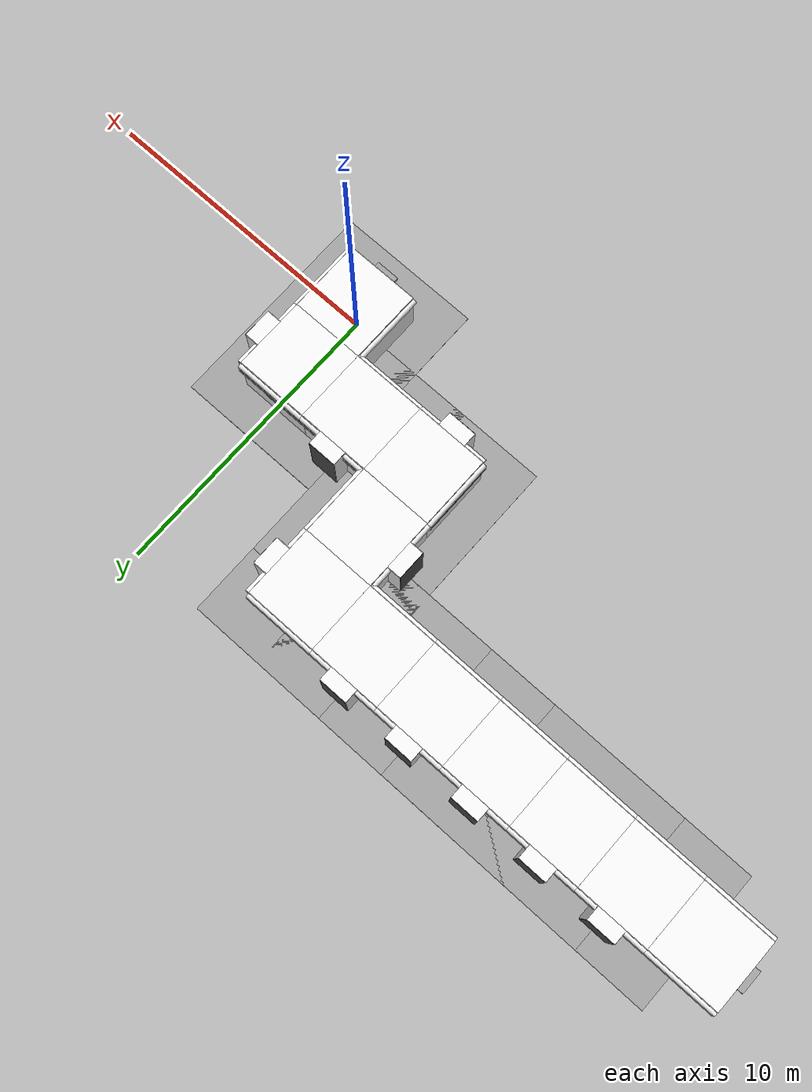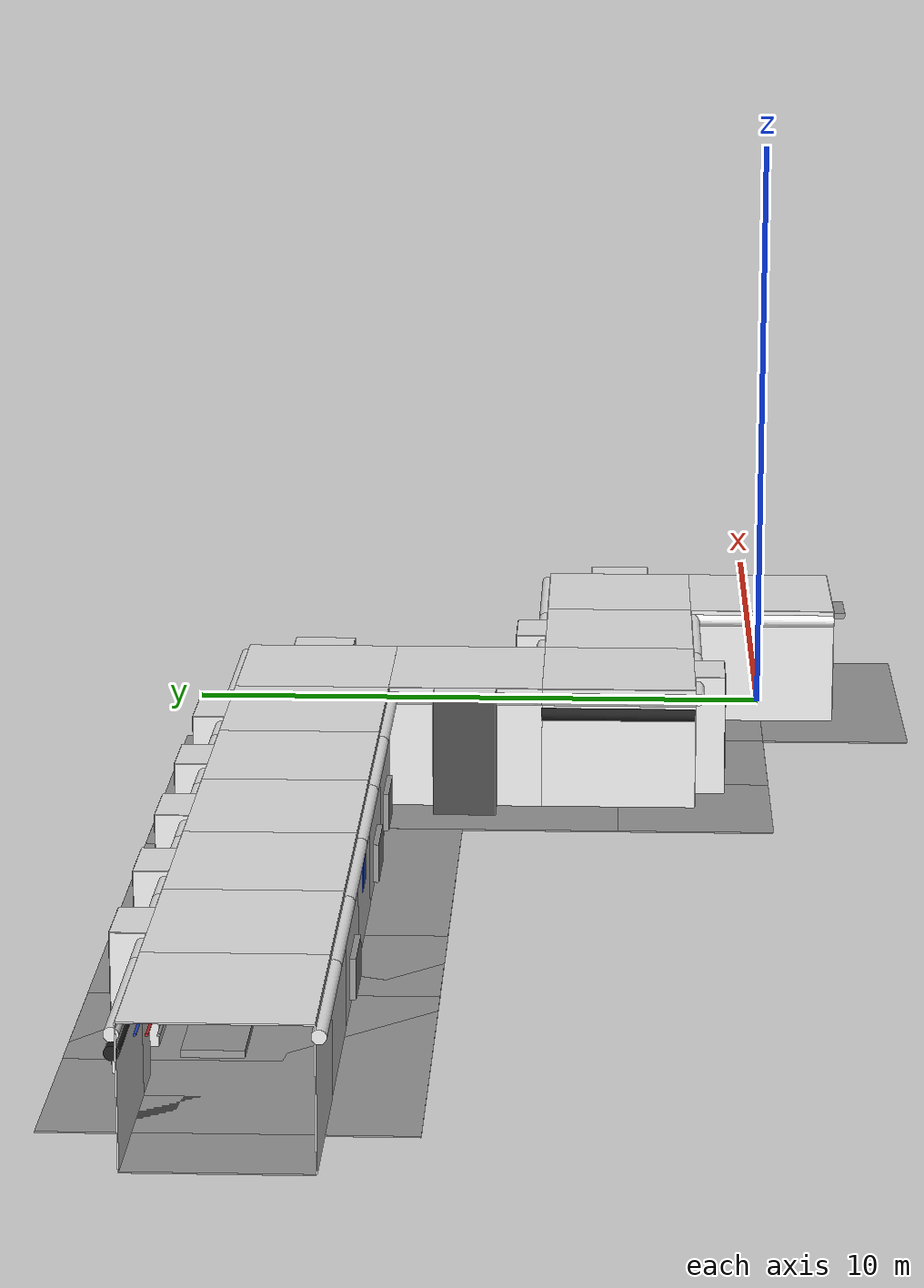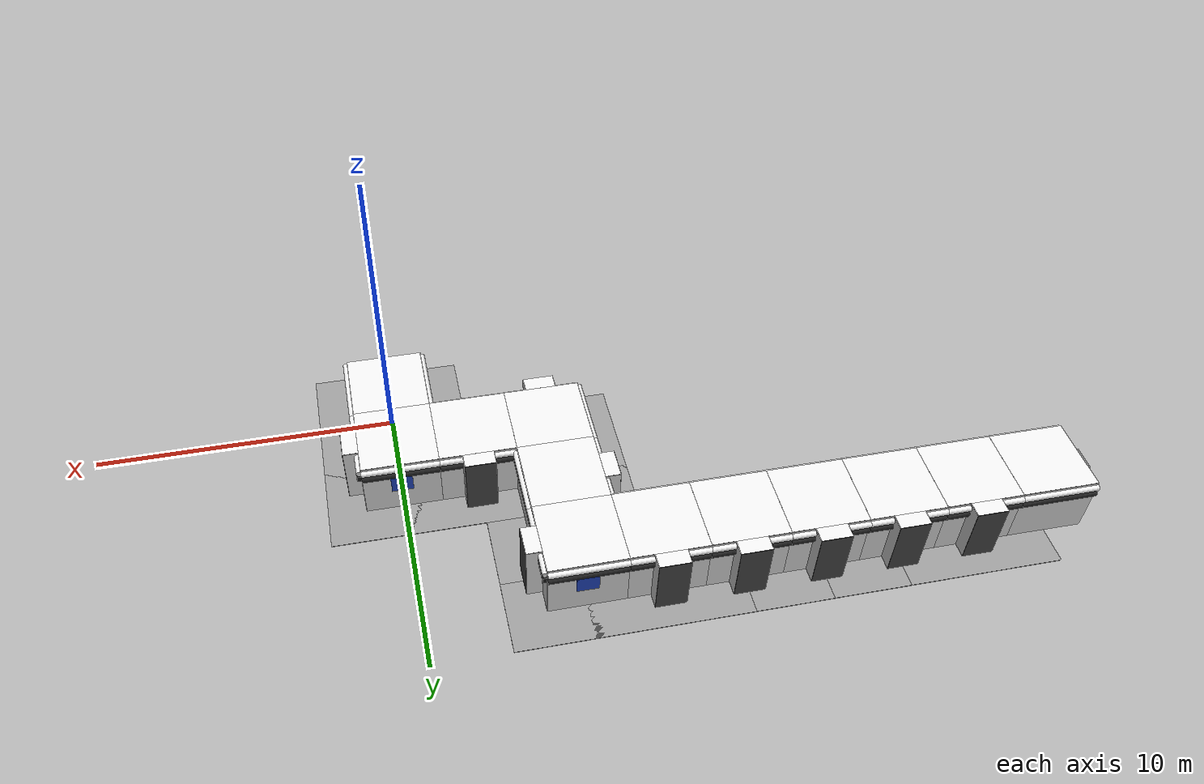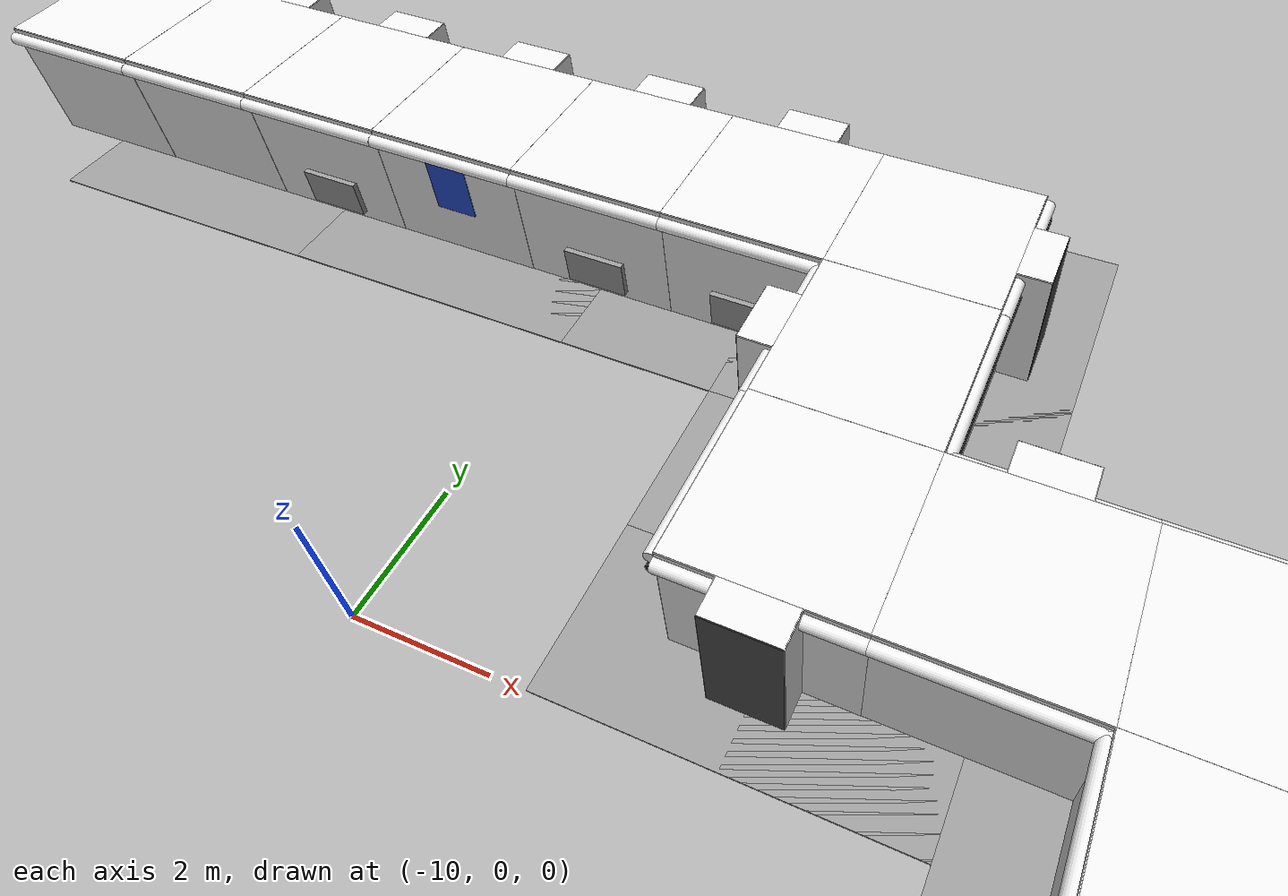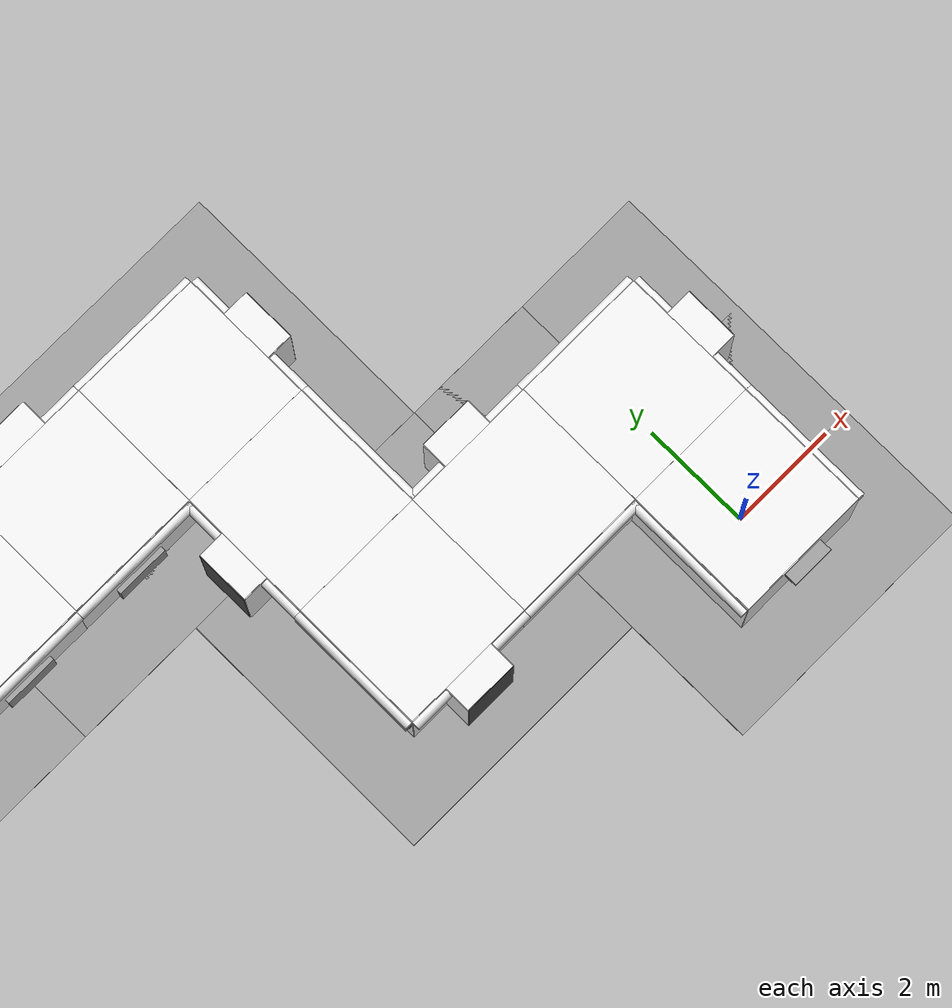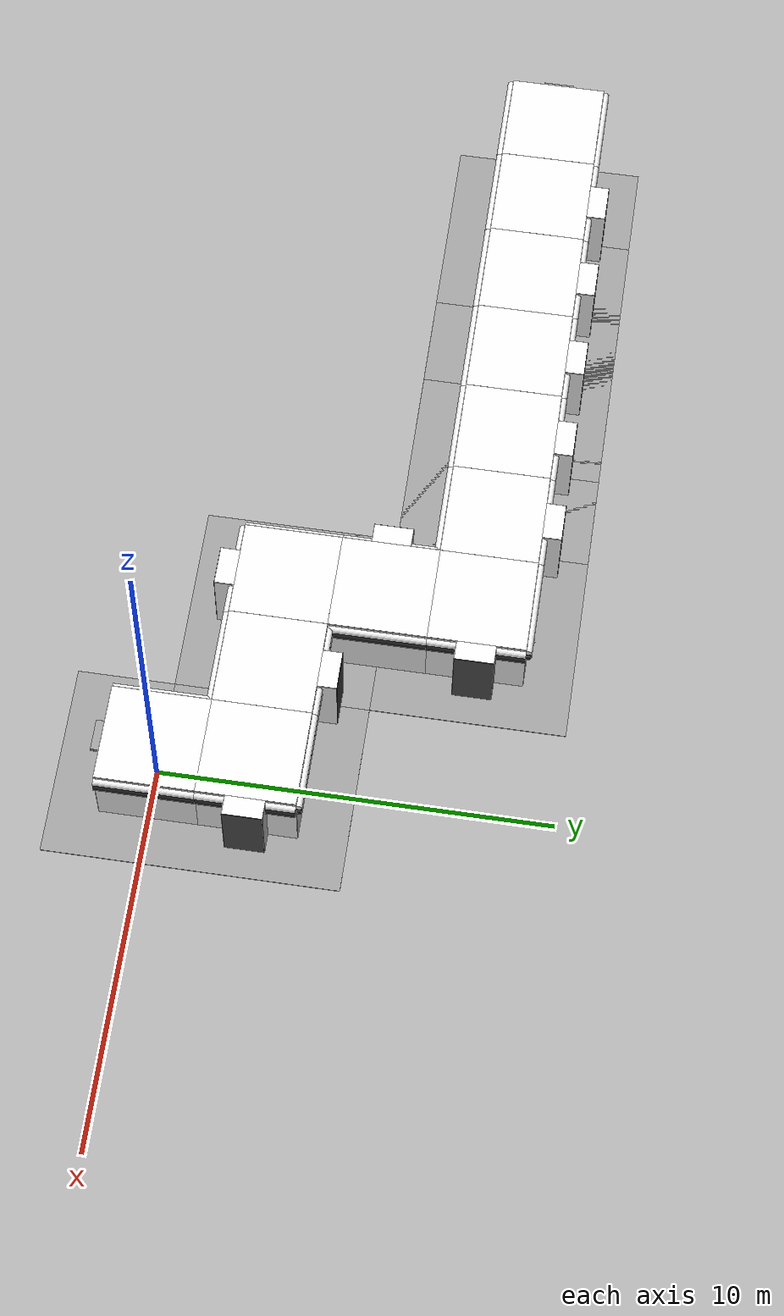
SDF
<sdf version="1.6">
 <world name="default">
  <gravity>0 0 -9.8</gravity>
  <magnetic_field>6e-06 2.3e-05 -4.2e-05</magnetic_field>
  <atmosphere type="adiabatic"/>
  <physics default="0" name="default_physics" type="ode">
   <max_step_size>0.001</max_step_size>
   <real_time_factor>1</real_time_factor>
   <real_time_update_rate>1000</real_time_update_rate>
  </physics>
  <scene><ambient>0.4 0.4 0.4 1</ambient><background>0.7 0.7 0.7 1</background><shadows>0</shadows></scene>
  <spherical_coordinates>
   <surface_model>EARTH_WGS84</surface_model>
   <latitude_deg>0</latitude_deg>
   <longitude_deg>0</longitude_deg>
   <elevation>0</elevation>
   <heading_deg>0</heading_deg>
  </spherical_coordinates>
  <model name="wall_back_0_0_0_0">
   <static>1</static>
   <pose>0.0 -1.25 1.0 0.0 0.0 0.0</pose>
   <link name="link">
    <collision name="collision"><geometry><box><size>2.5 0.02 2.0</size></box></geometry></collision>
    <visual name="visual">
     <material>
      <script><name>Gazebo/White</name><uri>file://media/materials/scripts/gazebo.material</uri></script>
     </material>
     <geometry><box><size>2.5 0.02 2.0</size></box></geometry>
    </visual>
   </link>
  </model>
  <model name="wall_right_0_0_0_0">
   <static>1</static>
   <pose>1.25 0.0 1.0 0.0 0.0 1.57</pose>
   <link name="link">
    <collision name="collision"><geometry><box><size>2.5 0.02 2.0</size></box></geometry></collision>
    <visual name="visual">
     <material>
      <script><name>Gazebo/White</name><uri>file://media/materials/scripts/gazebo.material</uri></script>
     </material>
     <geometry><box><size>2.5 0.02 2.0</size></box></geometry>
    </visual>
   </link>
  </model>
  <model name="wall_left_0_0_0_0">
   <static>1</static>
   <pose>-1.25 0.0 1.0 0.0 0.0 1.57</pose>
   <link name="link">
    <collision name="collision"><geometry><box><size>2.5 0.02 2.0</size></box></geometry></collision>
    <visual name="visual">
     <material>
      <script><name>Gazebo/White</name><uri>file://media/materials/scripts/gazebo.material</uri></script>
     </material>
     <geometry><box><size>2.5 0.02 2.0</size></box></geometry>
    </visual>
   </link>
  </model>
  <model name="wall_top_0_0_0_0">
   <static>1</static>
   <pose>0.0 0.0 2.0 1.57 0.0 0.0</pose>
   <link name="link">
    <collision name="collision"><geometry><box><size>2.5 0.02 2.5</size></box></geometry></collision>
    <visual name="visual">
     <material>
      <script><name>Gazebo/White</name><uri>file://media/materials/scripts/gazebo.material</uri></script>
     </material>
     <geometry><box><size>2.5 0.02 2.5</size></box></geometry>
    </visual>
   </link>
  </model>
  <light name="lightball_0_0_0_0_0" type="point">
   <cast_shadows>0</cast_shadows>
   <pose>-0.25 -0.25 1.99 0.0 0.0 0.0</pose>
   <diffuse>10 10 10 255</diffuse>
   <specular>10 10 10 255</specular>
  </light>
  <light name="lightball_1_0_0_0_0" type="point">
   <cast_shadows>0</cast_shadows>
   <pose>0.25 -0.25 1.99 0.0 0.0 0.0</pose>
   <diffuse>10 10 10 255</diffuse>
   <specular>10 10 10 255</specular>
  </light>
  <light name="lightball_2_0_0_0_0" type="point">
   <cast_shadows>0</cast_shadows>
   <pose>-0.25 0.25 1.99 0.0 0.0 0.0</pose>
   <diffuse>10 10 10 255</diffuse>
   <specular>10 10 10 255</specular>
  </light>
  <light name="lightball_3_0_0_0_0" type="point">
   <cast_shadows>0</cast_shadows>
   <pose>0.25 0.25 1.99 0.0 0.0 0.0</pose>
   <diffuse>10 10 10 255</diffuse>
   <specular>10 10 10 255</specular>
  </light>
  <model name="ceiling_1_0_0_0_0">
   <pose>0.0 0.0 1.7 0.0 0.0 0.0</pose>
   <link name="link_1">
    <visual name="visual">
     <geometry><box><size>0.8 1 0.1</size></box></geometry>
     <material>
      <script><uri>file://media/materials/scripts/gazebo.material</uri><name>Gazebo/Grey</name></script>
     </material>
    </visual>
    <collision name="collision"><geometry><box><size>0.8 1 0.1</size></box></geometry></collision>
   </link>
   <static>1</static>
  </model>
  <model name="ceiling_1_0_0_1_0">
   <pose>0.0 -1.0 1.7 0.0 0.0 0.0</pose>
   <link name="link_1">
    <visual name="visual">
     <geometry><box><size>0.8 1 0.1</size></box></geometry>
     <material>
      <script><uri>file://media/materials/scripts/gazebo.material</uri><name>Gazebo/Grey</name></script>
     </material>
    </visual>
    <collision name="collision"><geometry><box><size>0.8 1 0.1</size></box></geometry></collision>
   </link>
   <static>1</static>
  </model>
  <model name="ceiling_1_0_0_2_0">
   <pose>0.0 1.0 1.7 0.0 0.0 0.0</pose>
   <link name="link_1">
    <visual name="visual">
     <geometry><box><size>0.8 1 0.1</size></box></geometry>
     <material>
      <script><uri>file://media/materials/scripts/gazebo.material</uri><name>Gazebo/Grey</name></script>
     </material>
    </visual>
    <collision name="collision"><geometry><box><size>0.8 1 0.1</size></box></geometry></collision>
   </link>
   <static>1</static>
  </model>
  <model name="white_pipe_left_0_0_0_0">
   <static>1</static>
   <pose>0.0 0.0 1.84 0.0 0.0 0.0</pose>
   <link name="link_0">
    <visual name="visual">
     <pose>-1.3 0 0 1.57 0 0</pose>
     <geometry><cylinder><radius>0.1</radius><length>2.5</length></cylinder></geometry>
     <material>
      <script><uri>file://media/materials/scripts/gazebo.material</uri><name>Gazebo/White</name></script>
     </material>
    </visual>
    <collision name="collision">
     <pose>-1.3 0 0 1.57 0 0</pose>
     <geometry><cylinder><radius>0.1</radius><length>2.5</length></cylinder></geometry>
    </collision>
   </link>
  </model>
  <model name="white_pipe_right_0_0_0_0">
   <static>1</static>
   <pose>0.0 0.0 1.84 0.0 0.0 0.0</pose>
   <link name="link_0">
    <visual name="visual">
     <pose>1.3 0 0 1.57 0 0</pose>
     <geometry><cylinder><radius>0.1</radius><length>2.5</length></cylinder></geometry>
     <material>
      <script><uri>file://media/materials/scripts/gazebo.material</uri><name>Gazebo/White</name></script>
     </material>
    </visual>
    <collision name="collision">
     <pose>1.3 0 0 1.57 0 0</pose>
     <geometry><cylinder><radius>0.1</radius><length>2.5</length></cylinder></geometry>
    </collision>
   </link>
  </model>
  <model name="black_pipe_right_0_0_0_0">
   <static>1</static>
   <pose>0.0 0.0 1.84 0.0 0.0 0.0</pose>
   <link name="link_0">
    <visual name="visual">
     <pose>1.3 0 -0.25 1.57 0 0</pose>
     <geometry><cylinder><radius>0.1</radius><length>2.5</length></cylinder></geometry>
     <material>
      <script><uri>file://media/materials/scripts/gazebo.material</uri><name>Gazebo/Black</name></script>
     </material>
    </visual>
    <collision name="collision">
     <pose>1.3 0 -0.25 1.57 0 0</pose>
     <geometry><cylinder><radius>0.1</radius><length>2.5</length></cylinder></geometry>
    </collision>
   </link>
  </model>
  <model name="grey_pipe_right_0_0_0_0">
   <static>1</static>
   <pose>0.0 0.0 1.84 0.0 0.0 0.0</pose>
   <link name="link_0">
    <visual name="visual">
     <pose>0.7 0 0 1.57 0 0</pose>
     <geometry><cylinder><radius>0.02</radius><length>2.5</length></cylinder></geometry>
     <material>
      <script><uri>file://media/materials/scripts/gazebo.material</uri><name>Gazebo/Grey</name></script>
     </material>
    </visual>
    <collision name="collision">
     <pose>0.7 0 0 1.57 0 0</pose>
     <geometry><cylinder><radius>0.02</radius><length>2.5</length></cylinder></geometry>
    </collision>
   </link>
  </model>
  <model name="red_pipe_right_0_0_0_0">
   <static>1</static>
   <pose>0.0 0.0 1.84 0.0 0.0 0.0</pose>
   <link name="link_0">
    <visual name="visual">
     <pose>0.85 0 0 1.57 0 0</pose>
     <geometry><cylinder><radius>0.02</radius><length>2.5</length></cylinder></geometry>
     <material>
      <script><uri>file://media/materials/scripts/gazebo.material</uri><name>Gazebo/Red</name></script>
     </material>
    </visual>
    <collision name="collision">
     <pose>0.85 0 0 1.57 0 0</pose>
     <geometry><cylinder><radius>0.02</radius><length>2.5</length></cylinder></geometry>
    </collision>
   </link>
  </model>
  <model name="blue_pipe_right_0_0_0_0">
   <static>1</static>
   <pose>0.0 0.0 1.84 0.0 0.0 0.0</pose>
   <link name="link_0">
    <visual name="visual">
     <pose>1 0 0 1.57 0 0</pose>
     <geometry><cylinder><radius>0.02</radius><length>2.5</length></cylinder></geometry>
     <material>
      <script><uri>file://media/materials/scripts/gazebo.material</uri><name>Gazebo/Blue</name></script>
     </material>
    </visual>
    <collision name="collision">
     <pose>1 0 0 1.57 0 0</pose>
     <geometry><cylinder><radius>0.02</radius><length>2.5</length></cylinder></geometry>
    </collision>
   </link>
  </model>
  <model name="wall_bottom_0_0_0_0">
   <static>1</static>
   <link name="link">
    <collision name="collision"><geometry><box><size>5.0 5.0 0.02</size></box></geometry></collision>
    <visual name="visual">
     <material>
      <script><name>Gazebo/Grey</name><uri>file://media/materials/scripts/gazebo.material</uri></script>
     </material>
     <geometry><box><size>5.0 5.0 0.02</size></box></geometry>
    </visual>
   </link>
  </model>
  <model name="wall_front_0_1_0_3">
   <static>1</static>
   <pose>0.0 3.75 1.0 0.0 0.0 0.0</pose>
   <link name="link">
    <collision name="collision"><geometry><box><size>2.5 0.02 2.0</size></box></geometry></collision>
    <visual name="visual">
     <material>
      <script><name>Gazebo/White</name><uri>file://media/materials/scripts/gazebo.material</uri></script>
     </material>
     <geometry><box><size>2.5 0.02 2.0</size></box></geometry>
    </visual>
   </link>
  </model>
  <model name="wall_top_0_1_0_3">
   <static>1</static>
   <pose>0.0 2.5 2.0 1.57 0.0 0.0</pose>
   <link name="link">
    <collision name="collision"><geometry><box><size>2.5 0.02 2.5</size></box></geometry></collision>
    <visual name="visual">
     <material>
      <script><name>Gazebo/White</name><uri>file://media/materials/scripts/gazebo.material</uri></script>
     </material>
     <geometry><box><size>2.5 0.02 2.5</size></box></geometry>
    </visual>
   </link>
  </model>
  <light name="lightball_0_0_1_0_3" type="point">
   <cast_shadows>0</cast_shadows>
   <pose>-0.25 2.25 1.99 0.0 0.0 0.0</pose>
   <diffuse>10 10 10 255</diffuse>
   <specular>10 10 10 255</specular>
  </light>
  <light name="lightball_1_0_1_0_3" type="point">
   <cast_shadows>0</cast_shadows>
   <pose>0.25 2.25 1.99 0.0 0.0 0.0</pose>
   <diffuse>10 10 10 255</diffuse>
   <specular>10 10 10 255</specular>
  </light>
  <light name="lightball_2_0_1_0_3" type="point">
   <cast_shadows>0</cast_shadows>
   <pose>-0.25 2.75 1.99 0.0 0.0 0.0</pose>
   <diffuse>10 10 10 255</diffuse>
   <specular>10 10 10 255</specular>
  </light>
  <light name="lightball_3_0_1_0_3" type="point">
   <cast_shadows>0</cast_shadows>
   <pose>0.25 2.75 1.99 0.0 0.0 0.0</pose>
   <diffuse>10 10 10 255</diffuse>
   <specular>10 10 10 255</specular>
  </light>
  <model name="ceiling_1_0_1_0_3">
   <pose>0.0 1.5 1.7 0.0 0.0 0.0</pose>
   <link name="link_1">
    <visual name="visual">
     <geometry><box><size>0.8 1 0.1</size></box></geometry>
     <material>
      <script><uri>file://media/materials/scripts/gazebo.material</uri><name>Gazebo/Grey</name></script>
     </material>
    </visual>
    <collision name="collision"><geometry><box><size>0.8 1 0.1</size></box></geometry></collision>
   </link>
   <static>1</static>
  </model>
  <model name="ceiling_1_0_1_1_3">
   <pose>-1.0 2.5 1.7 0.0 0.0 1.57</pose>
   <link name="link_1">
    <visual name="visual">
     <geometry><box><size>0.8 1 0.1</size></box></geometry>
     <material>
      <script><uri>file://media/materials/scripts/gazebo.material</uri><name>Gazebo/Grey</name></script>
     </material>
    </visual>
    <collision name="collision"><geometry><box><size>0.8 1 0.1</size></box></geometry></collision>
   </link>
   <static>1</static>
  </model>
  <model name="white_pipe_left_0_1_0_3">
   <static>1</static>
   <pose>0.0 2.5 1.84 0.0 0.0 0.0</pose>
   <link name="link_0">
    <visual name="visual">
     <pose>-1.3 0 0 1.57 0 0</pose>
     <geometry><cylinder><radius>0.1</radius><length>2.5</length></cylinder></geometry>
     <material>
      <script><uri>file://media/materials/scripts/gazebo.material</uri><name>Gazebo/White</name></script>
     </material>
    </visual>
    <collision name="collision">
     <pose>-1.3 0 0 1.57 0 0</pose>
     <geometry><cylinder><radius>0.1</radius><length>2.5</length></cylinder></geometry>
    </collision>
   </link>
  </model>
  <model name="white_pipe_right_0_1_0_3">
   <static>1</static>
   <pose>0.0 2.5 1.84 0.0 0.0 0.0</pose>
   <link name="link_0">
    <visual name="visual">
     <pose>1.3 0 0 1.57 0 0</pose>
     <geometry><cylinder><radius>0.1</radius><length>2.5</length></cylinder></geometry>
     <material>
      <script><uri>file://media/materials/scripts/gazebo.material</uri><name>Gazebo/White</name></script>
     </material>
    </visual>
    <collision name="collision">
     <pose>1.3 0 0 1.57 0 0</pose>
     <geometry><cylinder><radius>0.1</radius><length>2.5</length></cylinder></geometry>
    </collision>
   </link>
  </model>
  <model name="black_pipe_right_0_1_0_3">
   <static>1</static>
   <pose>0.0 2.5 1.84 0.0 0.0 0.0</pose>
   <link name="link_0">
    <visual name="visual">
     <pose>1.3 0 -0.25 1.57 0 0</pose>
     <geometry><cylinder><radius>0.1</radius><length>2.5</length></cylinder></geometry>
     <material>
      <script><uri>file://media/materials/scripts/gazebo.material</uri><name>Gazebo/Black</name></script>
     </material>
    </visual>
    <collision name="collision">
     <pose>1.3 0 -0.25 1.57 0 0</pose>
     <geometry><cylinder><radius>0.1</radius><length>2.5</length></cylinder></geometry>
    </collision>
   </link>
  </model>
  <model name="grey_pipe_right_0_1_0_3">
   <static>1</static>
   <pose>0.0 2.5 1.84 0.0 0.0 0.0</pose>
   <link name="link_0">
    <visual name="visual">
     <pose>0.7 0 0 1.57 0 0</pose>
     <geometry><cylinder><radius>0.02</radius><length>2.5</length></cylinder></geometry>
     <material>
      <script><uri>file://media/materials/scripts/gazebo.material</uri><name>Gazebo/Grey</name></script>
     </material>
    </visual>
    <collision name="collision">
     <pose>0.7 0 0 1.57 0 0</pose>
     <geometry><cylinder><radius>0.02</radius><length>2.5</length></cylinder></geometry>
    </collision>
   </link>
  </model>
  <model name="red_pipe_right_0_1_0_3">
   <static>1</static>
   <pose>0.0 2.5 1.84 0.0 0.0 0.0</pose>
   <link name="link_0">
    <visual name="visual">
     <pose>0.85 0 0 1.57 0 0</pose>
     <geometry><cylinder><radius>0.02</radius><length>2.5</length></cylinder></geometry>
     <material>
      <script><uri>file://media/materials/scripts/gazebo.material</uri><name>Gazebo/Red</name></script>
     </material>
    </visual>
    <collision name="collision">
     <pose>0.85 0 0 1.57 0 0</pose>
     <geometry><cylinder><radius>0.02</radius><length>2.5</length></cylinder></geometry>
    </collision>
   </link>
  </model>
  <model name="blue_pipe_right_0_1_0_3">
   <static>1</static>
   <pose>0.0 2.5 1.84 0.0 0.0 0.0</pose>
   <link name="link_0">
    <visual name="visual">
     <pose>1 0 0 1.57 0 0</pose>
     <geometry><cylinder><radius>0.02</radius><length>2.5</length></cylinder></geometry>
     <material>
      <script><uri>file://media/materials/scripts/gazebo.material</uri><name>Gazebo/Blue</name></script>
     </material>
    </visual>
    <collision name="collision">
     <pose>1 0 0 1.57 0 0</pose>
     <geometry><cylinder><radius>0.02</radius><length>2.5</length></cylinder></geometry>
    </collision>
   </link>
  </model>
  <model name="white_pipe_left_1_0_1_0_3">
   <static>1</static>
   <pose>0.0 2.5 1.84 0.0 0.0 1.57</pose>
   <link name="link_0">
    <visual name="visual">
     <pose>-1.3 0 0 1.57 0 0</pose>
     <geometry><cylinder><radius>0.1</radius><length>2.5</length></cylinder></geometry>
     <material>
      <script><uri>file://media/materials/scripts/gazebo.material</uri><name>Gazebo/White</name></script>
     </material>
    </visual>
    <collision name="collision">
     <pose>-1.3 0 0 1.57 0 0</pose>
     <geometry><cylinder><radius>0.1</radius><length>2.5</length></cylinder></geometry>
    </collision>
   </link>
  </model>
  <model name="white_pipe_right_1_0_1_0_3">
   <static>1</static>
   <pose>0.0 2.5 1.84 0.0 0.0 1.57</pose>
   <link name="link_0">
    <visual name="visual">
     <pose>1.3 0 0 1.57 0 0</pose>
     <geometry><cylinder><radius>0.1</radius><length>2.5</length></cylinder></geometry>
     <material>
      <script><uri>file://media/materials/scripts/gazebo.material</uri><name>Gazebo/White</name></script>
     </material>
    </visual>
    <collision name="collision">
     <pose>1.3 0 0 1.57 0 0</pose>
     <geometry><cylinder><radius>0.1</radius><length>2.5</length></cylinder></geometry>
    </collision>
   </link>
  </model>
  <model name="black_pipe_right_1_0_1_0_3">
   <static>1</static>
   <pose>0.0 2.5 1.84 0.0 0.0 1.57</pose>
   <link name="link_0">
    <visual name="visual">
     <pose>1.3 0 -0.25 1.57 0 0</pose>
     <geometry><cylinder><radius>0.1</radius><length>2.5</length></cylinder></geometry>
     <material>
      <script><uri>file://media/materials/scripts/gazebo.material</uri><name>Gazebo/Black</name></script>
     </material>
    </visual>
    <collision name="collision">
     <pose>1.3 0 -0.25 1.57 0 0</pose>
     <geometry><cylinder><radius>0.1</radius><length>2.5</length></cylinder></geometry>
    </collision>
   </link>
  </model>
  <model name="grey_pipe_right_1_0_1_0_3">
   <static>1</static>
   <pose>0.0 2.5 1.84 0.0 0.0 1.57</pose>
   <link name="link_0">
    <visual name="visual">
     <pose>0.7 0 0 1.57 0 0</pose>
     <geometry><cylinder><radius>0.02</radius><length>2.5</length></cylinder></geometry>
     <material>
      <script><uri>file://media/materials/scripts/gazebo.material</uri><name>Gazebo/Grey</name></script>
     </material>
    </visual>
    <collision name="collision">
     <pose>0.7 0 0 1.57 0 0</pose>
     <geometry><cylinder><radius>0.02</radius><length>2.5</length></cylinder></geometry>
    </collision>
   </link>
  </model>
  <model name="red_pipe_right_1_0_1_0_3">
   <static>1</static>
   <pose>0.0 2.5 1.84 0.0 0.0 1.57</pose>
   <link name="link_0">
    <visual name="visual">
     <pose>0.85 0 0 1.57 0 0</pose>
     <geometry><cylinder><radius>0.02</radius><length>2.5</length></cylinder></geometry>
     <material>
      <script><uri>file://media/materials/scripts/gazebo.material</uri><name>Gazebo/Red</name></script>
     </material>
    </visual>
    <collision name="collision">
     <pose>0.85 0 0 1.57 0 0</pose>
     <geometry><cylinder><radius>0.02</radius><length>2.5</length></cylinder></geometry>
    </collision>
   </link>
  </model>
  <model name="blue_pipe_right_1_0_1_0_3">
   <static>1</static>
   <pose>0.0 2.5 1.84 0.0 0.0 1.57</pose>
   <link name="link_0">
    <visual name="visual">
     <pose>1 0 0 1.57 0 0</pose>
     <geometry><cylinder><radius>0.02</radius><length>2.5</length></cylinder></geometry>
     <material>
      <script><uri>file://media/materials/scripts/gazebo.material</uri><name>Gazebo/Blue</name></script>
     </material>
    </visual>
    <collision name="collision">
     <pose>1 0 0 1.57 0 0</pose>
     <geometry><cylinder><radius>0.02</radius><length>2.5</length></cylinder></geometry>
    </collision>
   </link>
  </model>
  <model name="panel_0_1_0_3">
   <static>1</static>
   <pose>0.0 3.75 1.3 0.0 0.0 1.57</pose>
   <link name="link">
    <collision name="collision"><geometry><box><size>0.04 0.7 1</size></box></geometry></collision>
    <visual name="visual">
     <material>
      <script><name>Gazebo/Blue</name><uri>file://media/materials/scripts/gazebo.material</uri></script>
     </material>
     <geometry><box><size>0.04 0.7 1</size></box></geometry>
    </visual>
   </link>
  </model>
  <model name="wall_right_front_left_0_1_0_3">
   <static>1</static>
   <pose>1.25 3.375 1.0 0.0 0.0 1.57</pose>
   <link name="link">
    <collision name="collision"><geometry><box><size>0.75 0.02 2.0</size></box></geometry></collision>
    <visual name="visual">
     <material>
      <script><name>Gazebo/White</name><uri>file://media/materials/scripts/gazebo.material</uri></script>
     </material>
     <geometry><box><size>0.75 0.02 2.0</size></box></geometry>
    </visual>
   </link>
  </model>
  <model name="wall_right_front_right_0_1_0_3">
   <static>1</static>
   <pose>1.25 1.625 1.0 0.0 0.0 1.57</pose>
   <link name="link">
    <collision name="collision"><geometry><box><size>0.75 0.02 2.0</size></box></geometry></collision>
    <visual name="visual">
     <material>
      <script><name>Gazebo/White</name><uri>file://media/materials/scripts/gazebo.material</uri></script>
     </material>
     <geometry><box><size>0.75 0.02 2.0</size></box></geometry>
    </visual>
   </link>
  </model>
  <model name="wall_right_front_up_0_1_0_3">
   <static>1</static>
   <pose>1.25 2.5 2.0 0.0 0.0 1.57</pose>
   <link name="link">
    <collision name="collision"><geometry><box><size>1.0 0.02 0.001</size></box></geometry></collision>
    <visual name="visual">
     <material>
      <script><name>Gazebo/White</name><uri>file://media/materials/scripts/gazebo.material</uri></script>
     </material>
     <geometry><box><size>1.0 0.02 0.001</size></box></geometry>
    </visual>
   </link>
  </model>
  <model name="wall_right_inside_back_0_1_0_3">
   <static>1</static>
   <pose>1.75 2.5 1.0 0.0 0.0 1.57</pose>
   <link name="link">
    <collision name="collision"><geometry><box><size>1 0.02 2</size></box></geometry></collision>
    <visual name="visual">
     <material>
      <script><name>Gazebo/DarkGrey</name><uri>file://media/materials/scripts/gazebo.material</uri></script>
     </material>
     <geometry><box><size>1 0.02 2</size></box></geometry>
    </visual>
   </link>
  </model>
  <model name="wall_right_inside_left_0_1_0_3">
   <static>1</static>
   <pose>1.5 3.0 1.0 0.0 0.0 0.0</pose>
   <link name="link">
    <collision name="collision"><geometry><box><size>0.5 0.02 2</size></box></geometry></collision>
    <visual name="visual">
     <material>
      <script><name>Gazebo/White</name><uri>file://media/materials/scripts/gazebo.material</uri></script>
     </material>
     <geometry><box><size>0.5 0.02 2</size></box></geometry>
    </visual>
   </link>
  </model>
  <model name="wall_right_inside_right_0_1_0_3">
   <static>1</static>
   <pose>1.5 2.0 1.0 0.0 0.0 0.0</pose>
   <link name="link">
    <collision name="collision"><geometry><box><size>0.5 0.02 2</size></box></geometry></collision>
    <visual name="visual">
     <material>
      <script><name>Gazebo/White</name><uri>file://media/materials/scripts/gazebo.material</uri></script>
     </material>
     <geometry><box><size>0.5 0.02 2</size></box></geometry>
    </visual>
   </link>
  </model>
  <model name="wall_right_inside_top_0_1_0_3">
   <static>1</static>
   <pose>1.5 2.5 2.0 1.57 0.0 1.57</pose>
   <link name="link">
    <collision name="collision"><geometry><box><size>1 0.02 0.5</size></box></geometry></collision>
    <visual name="visual">
     <material>
      <script><name>Gazebo/White</name><uri>file://media/materials/scripts/gazebo.material</uri></script>
     </material>
     <geometry><box><size>1 0.02 0.5</size></box></geometry>
    </visual>
   </link>
  </model>
  <model name="wall_bottom_0_1_0_3">
   <static>1</static>
   <pose>0.0 2.5 0.0 0.0 0.0 0.0</pose>
   <link name="link">
    <collision name="collision"><geometry><box><size>5.0 5.0 0.02</size></box></geometry></collision>
    <visual name="visual">
     <material>
      <script><name>Gazebo/Grey</name><uri>file://media/materials/scripts/gazebo.material</uri></script>
     </material>
     <geometry><box><size>5.0 5.0 0.02</size></box></geometry>
    </visual>
   </link>
  </model>
  <model name="wall_left_-1_1_0_1">
   <static>1</static>
   <pose>-2.5 1.25 1.0 0.0 0.0 3.14</pose>
   <link name="link">
    <collision name="collision"><geometry><box><size>2.5 0.02 2.0</size></box></geometry></collision>
    <visual name="visual">
     <material>
      <script><name>Gazebo/White</name><uri>file://media/materials/scripts/gazebo.material</uri></script>
     </material>
     <geometry><box><size>2.5 0.02 2.0</size></box></geometry>
    </visual>
   </link>
  </model>
  <model name="wall_top_-1_1_0_1">
   <static>1</static>
   <pose>-2.5 2.5 2.0 1.57 0.0 1.57</pose>
   <link name="link">
    <collision name="collision"><geometry><box><size>2.5 0.02 2.5</size></box></geometry></collision>
    <visual name="visual">
     <material>
      <script><name>Gazebo/White</name><uri>file://media/materials/scripts/gazebo.material</uri></script>
     </material>
     <geometry><box><size>2.5 0.02 2.5</size></box></geometry>
    </visual>
   </link>
  </model>
  <light name="lightball_0_-1_1_0_1" type="point">
   <cast_shadows>0</cast_shadows>
   <pose>-2.75 2.25 1.99 0.0 0.0 0.0</pose>
   <diffuse>10 10 10 255</diffuse>
   <specular>10 10 10 255</specular>
  </light>
  <light name="lightball_1_-1_1_0_1" type="point">
   <cast_shadows>0</cast_shadows>
   <pose>-2.25 2.25 1.99 0.0 0.0 0.0</pose>
   <diffuse>10 10 10 255</diffuse>
   <specular>10 10 10 255</specular>
  </light>
  <light name="lightball_2_-1_1_0_1" type="point">
   <cast_shadows>0</cast_shadows>
   <pose>-2.75 2.75 1.99 0.0 0.0 0.0</pose>
   <diffuse>10 10 10 255</diffuse>
   <specular>10 10 10 255</specular>
  </light>
  <light name="lightball_3_-1_1_0_1" type="point">
   <cast_shadows>0</cast_shadows>
   <pose>-2.25 2.75 1.99 0.0 0.0 0.0</pose>
   <diffuse>10 10 10 255</diffuse>
   <specular>10 10 10 255</specular>
  </light>
  <model name="ceiling_1_-1_1_0_1">
   <pose>-2.5 2.5 1.7 0.0 0.0 1.57</pose>
   <link name="link_1">
    <visual name="visual">
     <geometry><box><size>0.8 1 0.1</size></box></geometry>
     <material>
      <script><uri>file://media/materials/scripts/gazebo.material</uri><name>Gazebo/Grey</name></script>
     </material>
    </visual>
    <collision name="collision"><geometry><box><size>0.8 1 0.1</size></box></geometry></collision>
   </link>
   <static>1</static>
  </model>
  <model name="ceiling_1_-1_1_1_1">
   <pose>-1.5 2.5 1.7 0.0 0.0 1.57</pose>
   <link name="link_1">
    <visual name="visual">
     <geometry><box><size>0.8 1 0.1</size></box></geometry>
     <material>
      <script><uri>file://media/materials/scripts/gazebo.material</uri><name>Gazebo/Grey</name></script>
     </material>
    </visual>
    <collision name="collision"><geometry><box><size>0.8 1 0.1</size></box></geometry></collision>
   </link>
   <static>1</static>
  </model>
  <model name="ceiling_1_-1_1_2_1">
   <pose>-3.5 2.5 1.7 0.0 0.0 1.57</pose>
   <link name="link_1">
    <visual name="visual">
     <geometry><box><size>0.8 1 0.1</size></box></geometry>
     <material>
      <script><uri>file://media/materials/scripts/gazebo.material</uri><name>Gazebo/Grey</name></script>
     </material>
    </visual>
    <collision name="collision"><geometry><box><size>0.8 1 0.1</size></box></geometry></collision>
   </link>
   <static>1</static>
  </model>
  <model name="white_pipe_left_-1_1_0_1">
   <static>1</static>
   <pose>-2.5 2.5 1.84 0.0 0.0 1.57</pose>
   <link name="link_0">
    <visual name="visual">
     <pose>-1.3 0 0 1.57 0 0</pose>
     <geometry><cylinder><radius>0.1</radius><length>2.5</length></cylinder></geometry>
     <material>
      <script><uri>file://media/materials/scripts/gazebo.material</uri><name>Gazebo/White</name></script>
     </material>
    </visual>
    <collision name="collision">
     <pose>-1.3 0 0 1.57 0 0</pose>
     <geometry><cylinder><radius>0.1</radius><length>2.5</length></cylinder></geometry>
    </collision>
   </link>
  </model>
  <model name="white_pipe_right_-1_1_0_1">
   <static>1</static>
   <pose>-2.5 2.5 1.84 0.0 0.0 1.57</pose>
   <link name="link_0">
    <visual name="visual">
     <pose>1.3 0 0 1.57 0 0</pose>
     <geometry><cylinder><radius>0.1</radius><length>2.5</length></cylinder></geometry>
     <material>
      <script><uri>file://media/materials/scripts/gazebo.material</uri><name>Gazebo/White</name></script>
     </material>
    </visual>
    <collision name="collision">
     <pose>1.3 0 0 1.57 0 0</pose>
     <geometry><cylinder><radius>0.1</radius><length>2.5</length></cylinder></geometry>
    </collision>
   </link>
  </model>
  <model name="black_pipe_right_-1_1_0_1">
   <static>1</static>
   <pose>-2.5 2.5 1.84 0.0 0.0 1.57</pose>
   <link name="link_0">
    <visual name="visual">
     <pose>1.3 0 -0.25 1.57 0 0</pose>
     <geometry><cylinder><radius>0.1</radius><length>2.5</length></cylinder></geometry>
     <material>
      <script><uri>file://media/materials/scripts/gazebo.material</uri><name>Gazebo/Black</name></script>
     </material>
    </visual>
    <collision name="collision">
     <pose>1.3 0 -0.25 1.57 0 0</pose>
     <geometry><cylinder><radius>0.1</radius><length>2.5</length></cylinder></geometry>
    </collision>
   </link>
  </model>
  <model name="grey_pipe_right_-1_1_0_1">
   <static>1</static>
   <pose>-2.5 2.5 1.84 0.0 0.0 1.57</pose>
   <link name="link_0">
    <visual name="visual">
     <pose>0.7 0 0 1.57 0 0</pose>
     <geometry><cylinder><radius>0.02</radius><length>2.5</length></cylinder></geometry>
     <material>
      <script><uri>file://media/materials/scripts/gazebo.material</uri><name>Gazebo/Grey</name></script>
     </material>
    </visual>
    <collision name="collision">
     <pose>0.7 0 0 1.57 0 0</pose>
     <geometry><cylinder><radius>0.02</radius><length>2.5</length></cylinder></geometry>
    </collision>
   </link>
  </model>
  <model name="red_pipe_right_-1_1_0_1">
   <static>1</static>
   <pose>-2.5 2.5 1.84 0.0 0.0 1.57</pose>
   <link name="link_0">
    <visual name="visual">
     <pose>0.85 0 0 1.57 0 0</pose>
     <geometry><cylinder><radius>0.02</radius><length>2.5</length></cylinder></geometry>
     <material>
      <script><uri>file://media/materials/scripts/gazebo.material</uri><name>Gazebo/Red</name></script>
     </material>
    </visual>
    <collision name="collision">
     <pose>0.85 0 0 1.57 0 0</pose>
     <geometry><cylinder><radius>0.02</radius><length>2.5</length></cylinder></geometry>
    </collision>
   </link>
  </model>
  <model name="blue_pipe_right_-1_1_0_1">
   <static>1</static>
   <pose>-2.5 2.5 1.84 0.0 0.0 1.57</pose>
   <link name="link_0">
    <visual name="visual">
     <pose>1 0 0 1.57 0 0</pose>
     <geometry><cylinder><radius>0.02</radius><length>2.5</length></cylinder></geometry>
     <material>
      <script><uri>file://media/materials/scripts/gazebo.material</uri><name>Gazebo/Blue</name></script>
     </material>
    </visual>
    <collision name="collision">
     <pose>1 0 0 1.57 0 0</pose>
     <geometry><cylinder><radius>0.02</radius><length>2.5</length></cylinder></geometry>
    </collision>
   </link>
  </model>
  <model name="wall_right_front_left_-1_1_0_1">
   <static>1</static>
   <pose>-3.375 3.75 1.0 0.0 0.0 3.14</pose>
   <link name="link">
    <collision name="collision"><geometry><box><size>0.75 0.02 2.0</size></box></geometry></collision>
    <visual name="visual">
     <material>
      <script><name>Gazebo/White</name><uri>file://media/materials/scripts/gazebo.material</uri></script>
     </material>
     <geometry><box><size>0.75 0.02 2.0</size></box></geometry>
    </visual>
   </link>
  </model>
  <model name="wall_right_front_right_-1_1_0_1">
   <static>1</static>
   <pose>-1.625 3.75 1.0 0.0 0.0 3.14</pose>
   <link name="link">
    <collision name="collision"><geometry><box><size>0.75 0.02 2.0</size></box></geometry></collision>
    <visual name="visual">
     <material>
      <script><name>Gazebo/White</name><uri>file://media/materials/scripts/gazebo.material</uri></script>
     </material>
     <geometry><box><size>0.75 0.02 2.0</size></box></geometry>
    </visual>
   </link>
  </model>
  <model name="wall_right_front_up_-1_1_0_1">
   <static>1</static>
   <pose>-2.5 3.75 2.0 0.0 0.0 3.14</pose>
   <link name="link">
    <collision name="collision"><geometry><box><size>1.0 0.02 0.001</size></box></geometry></collision>
    <visual name="visual">
     <material>
      <script><name>Gazebo/White</name><uri>file://media/materials/scripts/gazebo.material</uri></script>
     </material>
     <geometry><box><size>1.0 0.02 0.001</size></box></geometry>
    </visual>
   </link>
  </model>
  <model name="wall_right_inside_back_-1_1_0_1">
   <static>1</static>
   <pose>-2.5 4.25 1.0 0.0 0.0 3.14</pose>
   <link name="link">
    <collision name="collision"><geometry><box><size>1 0.02 2</size></box></geometry></collision>
    <visual name="visual">
     <material>
      <script><name>Gazebo/DarkGrey</name><uri>file://media/materials/scripts/gazebo.material</uri></script>
     </material>
     <geometry><box><size>1 0.02 2</size></box></geometry>
    </visual>
   </link>
  </model>
  <model name="wall_right_inside_left_-1_1_0_1">
   <static>1</static>
   <pose>-3.0 4.0 1.0 0.0 0.0 1.57</pose>
   <link name="link">
    <collision name="collision"><geometry><box><size>0.5 0.02 2</size></box></geometry></collision>
    <visual name="visual">
     <material>
      <script><name>Gazebo/White</name><uri>file://media/materials/scripts/gazebo.material</uri></script>
     </material>
     <geometry><box><size>0.5 0.02 2</size></box></geometry>
    </visual>
   </link>
  </model>
  <model name="wall_right_inside_right_-1_1_0_1">
   <static>1</static>
   <pose>-2.0 4.0 1.0 0.0 0.0 1.57</pose>
   <link name="link">
    <collision name="collision"><geometry><box><size>0.5 0.02 2</size></box></geometry></collision>
    <visual name="visual">
     <material>
      <script><name>Gazebo/White</name><uri>file://media/materials/scripts/gazebo.material</uri></script>
     </material>
     <geometry><box><size>0.5 0.02 2</size></box></geometry>
    </visual>
   </link>
  </model>
  <model name="wall_right_inside_top_-1_1_0_1">
   <static>1</static>
   <pose>-2.5 4.0 2.0 1.57 0.0 3.14</pose>
   <link name="link">
    <collision name="collision"><geometry><box><size>1 0.02 0.5</size></box></geometry></collision>
    <visual name="visual">
     <material>
      <script><name>Gazebo/White</name><uri>file://media/materials/scripts/gazebo.material</uri></script>
     </material>
     <geometry><box><size>1 0.02 0.5</size></box></geometry>
    </visual>
   </link>
  </model>
  <model name="wall_bottom_-1_1_0_1">
   <static>1</static>
   <pose>-2.5 2.5 0.0 0.0 0.0 1.57</pose>
   <link name="link">
    <collision name="collision"><geometry><box><size>5.0 5.0 0.02</size></box></geometry></collision>
    <visual name="visual">
     <material>
      <script><name>Gazebo/Grey</name><uri>file://media/materials/scripts/gazebo.material</uri></script>
     </material>
     <geometry><box><size>5.0 5.0 0.02</size></box></geometry>
    </visual>
   </link>
  </model>
  <model name="wall_front_-2_1_0_2">
   <static>1</static>
   <pose>-6.25 2.5 1.0 0.0 0.0 1.57</pose>
   <link name="link">
    <collision name="collision"><geometry><box><size>2.5 0.02 2.0</size></box></geometry></collision>
    <visual name="visual">
     <material>
      <script><name>Gazebo/White</name><uri>file://media/materials/scripts/gazebo.material</uri></script>
     </material>
     <geometry><box><size>2.5 0.02 2.0</size></box></geometry>
    </visual>
   </link>
  </model>
  <model name="wall_top_-2_1_0_2">
   <static>1</static>
   <pose>-5.0 2.5 2.0 1.57 0.0 1.57</pose>
   <link name="link">
    <collision name="collision"><geometry><box><size>2.5 0.02 2.5</size></box></geometry></collision>
    <visual name="visual">
     <material>
      <script><name>Gazebo/White</name><uri>file://media/materials/scripts/gazebo.material</uri></script>
     </material>
     <geometry><box><size>2.5 0.02 2.5</size></box></geometry>
    </visual>
   </link>
  </model>
  <light name="lightball_0_-2_1_0_2" type="point">
   <cast_shadows>0</cast_shadows>
   <pose>-5.25 2.25 1.99 0.0 0.0 0.0</pose>
   <diffuse>10 10 10 255</diffuse>
   <specular>10 10 10 255</specular>
  </light>
  <light name="lightball_1_-2_1_0_2" type="point">
   <cast_shadows>0</cast_shadows>
   <pose>-4.75 2.25 1.99 0.0 0.0 0.0</pose>
   <diffuse>10 10 10 255</diffuse>
   <specular>10 10 10 255</specular>
  </light>
  <light name="lightball_2_-2_1_0_2" type="point">
   <cast_shadows>0</cast_shadows>
   <pose>-5.25 2.75 1.99 0.0 0.0 0.0</pose>
   <diffuse>10 10 10 255</diffuse>
   <specular>10 10 10 255</specular>
  </light>
  <light name="lightball_3_-2_1_0_2" type="point">
   <cast_shadows>0</cast_shadows>
   <pose>-4.75 2.75 1.99 0.0 0.0 0.0</pose>
   <diffuse>10 10 10 255</diffuse>
   <specular>10 10 10 255</specular>
  </light>
  <model name="ceiling_1_-2_1_0_2">
   <pose>-4.0 2.5 1.7 0.0 0.0 1.57</pose>
   <link name="link_1">
    <visual name="visual">
     <geometry><box><size>0.8 1 0.1</size></box></geometry>
     <material>
      <script><uri>file://media/materials/scripts/gazebo.material</uri><name>Gazebo/Grey</name></script>
     </material>
    </visual>
    <collision name="collision"><geometry><box><size>0.8 1 0.1</size></box></geometry></collision>
   </link>
   <static>1</static>
  </model>
  <model name="ceiling_1_-2_1_1_2">
   <pose>-5.0 3.5 1.7 0.0 0.0 3.14</pose>
   <link name="link_1">
    <visual name="visual">
     <geometry><box><size>0.8 1 0.1</size></box></geometry>
     <material>
      <script><uri>file://media/materials/scripts/gazebo.material</uri><name>Gazebo/Grey</name></script>
     </material>
    </visual>
    <collision name="collision"><geometry><box><size>0.8 1 0.1</size></box></geometry></collision>
   </link>
   <static>1</static>
  </model>
  <model name="white_pipe_left_-2_1_0_2">
   <static>1</static>
   <pose>-5.0 2.5 1.84 0.0 0.0 1.57</pose>
   <link name="link_0">
    <visual name="visual">
     <pose>-1.3 0 0 1.57 0 0</pose>
     <geometry><cylinder><radius>0.1</radius><length>2.5</length></cylinder></geometry>
     <material>
      <script><uri>file://media/materials/scripts/gazebo.material</uri><name>Gazebo/White</name></script>
     </material>
    </visual>
    <collision name="collision">
     <pose>-1.3 0 0 1.57 0 0</pose>
     <geometry><cylinder><radius>0.1</radius><length>2.5</length></cylinder></geometry>
    </collision>
   </link>
  </model>
  <model name="white_pipe_right_-2_1_0_2">
   <static>1</static>
   <pose>-5.0 2.5 1.84 0.0 0.0 1.57</pose>
   <link name="link_0">
    <visual name="visual">
     <pose>1.3 0 0 1.57 0 0</pose>
     <geometry><cylinder><radius>0.1</radius><length>2.5</length></cylinder></geometry>
     <material>
      <script><uri>file://media/materials/scripts/gazebo.material</uri><name>Gazebo/White</name></script>
     </material>
    </visual>
    <collision name="collision">
     <pose>1.3 0 0 1.57 0 0</pose>
     <geometry><cylinder><radius>0.1</radius><length>2.5</length></cylinder></geometry>
    </collision>
   </link>
  </model>
  <model name="black_pipe_right_-2_1_0_2">
   <static>1</static>
   <pose>-5.0 2.5 1.84 0.0 0.0 1.57</pose>
   <link name="link_0">
    <visual name="visual">
     <pose>1.3 0 -0.25 1.57 0 0</pose>
     <geometry><cylinder><radius>0.1</radius><length>2.5</length></cylinder></geometry>
     <material>
      <script><uri>file://media/materials/scripts/gazebo.material</uri><name>Gazebo/Black</name></script>
     </material>
    </visual>
    <collision name="collision">
     <pose>1.3 0 -0.25 1.57 0 0</pose>
     <geometry><cylinder><radius>0.1</radius><length>2.5</length></cylinder></geometry>
    </collision>
   </link>
  </model>
  <model name="grey_pipe_right_-2_1_0_2">
   <static>1</static>
   <pose>-5.0 2.5 1.84 0.0 0.0 1.57</pose>
   <link name="link_0">
    <visual name="visual">
     <pose>0.7 0 0 1.57 0 0</pose>
     <geometry><cylinder><radius>0.02</radius><length>2.5</length></cylinder></geometry>
     <material>
      <script><uri>file://media/materials/scripts/gazebo.material</uri><name>Gazebo/Grey</name></script>
     </material>
    </visual>
    <collision name="collision">
     <pose>0.7 0 0 1.57 0 0</pose>
     <geometry><cylinder><radius>0.02</radius><length>2.5</length></cylinder></geometry>
    </collision>
   </link>
  </model>
  <model name="red_pipe_right_-2_1_0_2">
   <static>1</static>
   <pose>-5.0 2.5 1.84 0.0 0.0 1.57</pose>
   <link name="link_0">
    <visual name="visual">
     <pose>0.85 0 0 1.57 0 0</pose>
     <geometry><cylinder><radius>0.02</radius><length>2.5</length></cylinder></geometry>
     <material>
      <script><uri>file://media/materials/scripts/gazebo.material</uri><name>Gazebo/Red</name></script>
     </material>
    </visual>
    <collision name="collision">
     <pose>0.85 0 0 1.57 0 0</pose>
     <geometry><cylinder><radius>0.02</radius><length>2.5</length></cylinder></geometry>
    </collision>
   </link>
  </model>
  <model name="blue_pipe_right_-2_1_0_2">
   <static>1</static>
   <pose>-5.0 2.5 1.84 0.0 0.0 1.57</pose>
   <link name="link_0">
    <visual name="visual">
     <pose>1 0 0 1.57 0 0</pose>
     <geometry><cylinder><radius>0.02</radius><length>2.5</length></cylinder></geometry>
     <material>
      <script><uri>file://media/materials/scripts/gazebo.material</uri><name>Gazebo/Blue</name></script>
     </material>
    </visual>
    <collision name="collision">
     <pose>1 0 0 1.57 0 0</pose>
     <geometry><cylinder><radius>0.02</radius><length>2.5</length></cylinder></geometry>
    </collision>
   </link>
  </model>
  <model name="white_pipe_left_1_-2_1_0_2">
   <static>1</static>
   <pose>-5.0 2.5 1.84 0.0 0.0 3.14</pose>
   <link name="link_0">
    <visual name="visual">
     <pose>-1.3 0 0 1.57 0 0</pose>
     <geometry><cylinder><radius>0.1</radius><length>2.5</length></cylinder></geometry>
     <material>
      <script><uri>file://media/materials/scripts/gazebo.material</uri><name>Gazebo/White</name></script>
     </material>
    </visual>
    <collision name="collision">
     <pose>-1.3 0 0 1.57 0 0</pose>
     <geometry><cylinder><radius>0.1</radius><length>2.5</length></cylinder></geometry>
    </collision>
   </link>
  </model>
  <model name="white_pipe_right_1_-2_1_0_2">
   <static>1</static>
   <pose>-5.0 2.5 1.84 0.0 0.0 3.14</pose>
   <link name="link_0">
    <visual name="visual">
     <pose>1.3 0 0 1.57 0 0</pose>
     <geometry><cylinder><radius>0.1</radius><length>2.5</length></cylinder></geometry>
     <material>
      <script><uri>file://media/materials/scripts/gazebo.material</uri><name>Gazebo/White</name></script>
     </material>
    </visual>
    <collision name="collision">
     <pose>1.3 0 0 1.57 0 0</pose>
     <geometry><cylinder><radius>0.1</radius><length>2.5</length></cylinder></geometry>
    </collision>
   </link>
  </model>
  <model name="black_pipe_right_1_-2_1_0_2">
   <static>1</static>
   <pose>-5.0 2.5 1.84 0.0 0.0 3.14</pose>
   <link name="link_0">
    <visual name="visual">
     <pose>1.3 0 -0.25 1.57 0 0</pose>
     <geometry><cylinder><radius>0.1</radius><length>2.5</length></cylinder></geometry>
     <material>
      <script><uri>file://media/materials/scripts/gazebo.material</uri><name>Gazebo/Black</name></script>
     </material>
    </visual>
    <collision name="collision">
     <pose>1.3 0 -0.25 1.57 0 0</pose>
     <geometry><cylinder><radius>0.1</radius><length>2.5</length></cylinder></geometry>
    </collision>
   </link>
  </model>
  <model name="grey_pipe_right_1_-2_1_0_2">
   <static>1</static>
   <pose>-5.0 2.5 1.84 0.0 0.0 3.14</pose>
   <link name="link_0">
    <visual name="visual">
     <pose>0.7 0 0 1.57 0 0</pose>
     <geometry><cylinder><radius>0.02</radius><length>2.5</length></cylinder></geometry>
     <material>
      <script><uri>file://media/materials/scripts/gazebo.material</uri><name>Gazebo/Grey</name></script>
     </material>
    </visual>
    <collision name="collision">
     <pose>0.7 0 0 1.57 0 0</pose>
     <geometry><cylinder><radius>0.02</radius><length>2.5</length></cylinder></geometry>
    </collision>
   </link>
  </model>
  <model name="red_pipe_right_1_-2_1_0_2">
   <static>1</static>
   <pose>-5.0 2.5 1.84 0.0 0.0 3.14</pose>
   <link name="link_0">
    <visual name="visual">
     <pose>0.85 0 0 1.57 0 0</pose>
     <geometry><cylinder><radius>0.02</radius><length>2.5</length></cylinder></geometry>
     <material>
      <script><uri>file://media/materials/scripts/gazebo.material</uri><name>Gazebo/Red</name></script>
     </material>
    </visual>
    <collision name="collision">
     <pose>0.85 0 0 1.57 0 0</pose>
     <geometry><cylinder><radius>0.02</radius><length>2.5</length></cylinder></geometry>
    </collision>
   </link>
  </model>
  <model name="blue_pipe_right_1_-2_1_0_2">
   <static>1</static>
   <pose>-5.0 2.5 1.84 0.0 0.0 3.14</pose>
   <link name="link_0">
    <visual name="visual">
     <pose>1 0 0 1.57 0 0</pose>
     <geometry><cylinder><radius>0.02</radius><length>2.5</length></cylinder></geometry>
     <material>
      <script><uri>file://media/materials/scripts/gazebo.material</uri><name>Gazebo/Blue</name></script>
     </material>
    </visual>
    <collision name="collision">
     <pose>1 0 0 1.57 0 0</pose>
     <geometry><cylinder><radius>0.02</radius><length>2.5</length></cylinder></geometry>
    </collision>
   </link>
  </model>
  <model name="wall_left_front_left_-2_1_0_2">
   <static>1</static>
   <pose>-5.875 1.25 1.0 0.0 0.0 3.14</pose>
   <link name="link">
    <collision name="collision"><geometry><box><size>0.75 0.02 2.0</size></box></geometry></collision>
    <visual name="visual">
     <material>
      <script><name>Gazebo/White</name><uri>file://media/materials/scripts/gazebo.material</uri></script>
     </material>
     <geometry><box><size>0.75 0.02 2.0</size></box></geometry>
    </visual>
   </link>
  </model>
  <model name="wall_left_front_right_-2_1_0_2">
   <static>1</static>
   <pose>-4.125 1.25 1.0 0.0 0.0 3.14</pose>
   <link name="link">
    <collision name="collision"><geometry><box><size>0.75 0.02 2.0</size></box></geometry></collision>
    <visual name="visual">
     <material>
      <script><name>Gazebo/White</name><uri>file://media/materials/scripts/gazebo.material</uri></script>
     </material>
     <geometry><box><size>0.75 0.02 2.0</size></box></geometry>
    </visual>
   </link>
  </model>
  <model name="wall_left_front_up_-2_1_0_2">
   <static>1</static>
   <pose>-5.0 1.25 2.0 0.0 0.0 3.14</pose>
   <link name="link">
    <collision name="collision"><geometry><box><size>1.0 0.02 0.001</size></box></geometry></collision>
    <visual name="visual">
     <material>
      <script><name>Gazebo/White</name><uri>file://media/materials/scripts/gazebo.material</uri></script>
     </material>
     <geometry><box><size>1.0 0.02 0.001</size></box></geometry>
    </visual>
   </link>
  </model>
  <model name="wall_left_inside_back_-2_1_0_2">
   <static>1</static>
   <pose>-5.0 0.75 1.0 0.0 0.0 3.14</pose>
   <link name="link">
    <collision name="collision"><geometry><box><size>1 0.02 2</size></box></geometry></collision>
    <visual name="visual">
     <material>
      <script><name>Gazebo/DarkGrey</name><uri>file://media/materials/scripts/gazebo.material</uri></script>
     </material>
     <geometry><box><size>1 0.02 2</size></box></geometry>
    </visual>
   </link>
  </model>
  <model name="wall_left_inside_left_-2_1_0_2">
   <static>1</static>
   <pose>-5.5 1.0 1.0 0.0 0.0 1.57</pose>
   <link name="link">
    <collision name="collision"><geometry><box><size>0.5 0.02 2</size></box></geometry></collision>
    <visual name="visual">
     <material>
      <script><name>Gazebo/White</name><uri>file://media/materials/scripts/gazebo.material</uri></script>
     </material>
     <geometry><box><size>0.5 0.02 2</size></box></geometry>
    </visual>
   </link>
  </model>
  <model name="wall_left_inside_right_-2_1_0_2">
   <static>1</static>
   <pose>-4.5 1.0 1.0 0.0 0.0 1.57</pose>
   <link name="link">
    <collision name="collision"><geometry><box><size>0.5 0.02 2</size></box></geometry></collision>
    <visual name="visual">
     <material>
      <script><name>Gazebo/White</name><uri>file://media/materials/scripts/gazebo.material</uri></script>
     </material>
     <geometry><box><size>0.5 0.02 2</size></box></geometry>
    </visual>
   </link>
  </model>
  <model name="wall_left_inside_top_-2_1_0_2">
   <static>1</static>
   <pose>-5.0 1.0 2.0 1.57 0.0 3.14</pose>
   <link name="link">
    <collision name="collision"><geometry><box><size>1 0.02 0.5</size></box></geometry></collision>
    <visual name="visual">
     <material>
      <script><name>Gazebo/White</name><uri>file://media/materials/scripts/gazebo.material</uri></script>
     </material>
     <geometry><box><size>1 0.02 0.5</size></box></geometry>
    </visual>
   </link>
  </model>
  <model name="wall_bottom_-2_1_0_2">
   <static>1</static>
   <pose>-5.0 2.5 0.0 0.0 0.0 1.57</pose>
   <link name="link">
    <collision name="collision"><geometry><box><size>5.0 5.0 0.02</size></box></geometry></collision>
    <visual name="visual">
     <material>
      <script><name>Gazebo/Grey</name><uri>file://media/materials/scripts/gazebo.material</uri></script>
     </material>
     <geometry><box><size>5.0 5.0 0.02</size></box></geometry>
    </visual>
   </link>
  </model>
  <model name="wall_right_-2_2_0_1">
   <static>1</static>
   <pose>-3.75 5.0 1.0 0.0 0.0 1.57</pose>
   <link name="link">
    <collision name="collision"><geometry><box><size>2.5 0.02 2.0</size></box></geometry></collision>
    <visual name="visual">
     <material>
      <script><name>Gazebo/White</name><uri>file://media/materials/scripts/gazebo.material</uri></script>
     </material>
     <geometry><box><size>2.5 0.02 2.0</size></box></geometry>
    </visual>
   </link>
  </model>
  <model name="wall_top_-2_2_0_1">
   <static>1</static>
   <pose>-5.0 5.0 2.0 1.57 0.0 0.0</pose>
   <link name="link">
    <collision name="collision"><geometry><box><size>2.5 0.02 2.5</size></box></geometry></collision>
    <visual name="visual">
     <material>
      <script><name>Gazebo/White</name><uri>file://media/materials/scripts/gazebo.material</uri></script>
     </material>
     <geometry><box><size>2.5 0.02 2.5</size></box></geometry>
    </visual>
   </link>
  </model>
  <light name="lightball_0_-2_2_0_1" type="point">
   <cast_shadows>0</cast_shadows>
   <pose>-5.25 4.75 1.99 0.0 0.0 0.0</pose>
   <diffuse>10 10 10 255</diffuse>
   <specular>10 10 10 255</specular>
  </light>
  <light name="lightball_1_-2_2_0_1" type="point">
   <cast_shadows>0</cast_shadows>
   <pose>-4.75 4.75 1.99 0.0 0.0 0.0</pose>
   <diffuse>10 10 10 255</diffuse>
   <specular>10 10 10 255</specular>
  </light>
  <light name="lightball_2_-2_2_0_1" type="point">
   <cast_shadows>0</cast_shadows>
   <pose>-5.25 5.25 1.99 0.0 0.0 0.0</pose>
   <diffuse>10 10 10 255</diffuse>
   <specular>10 10 10 255</specular>
  </light>
  <light name="lightball_3_-2_2_0_1" type="point">
   <cast_shadows>0</cast_shadows>
   <pose>-4.75 5.25 1.99 0.0 0.0 0.0</pose>
   <diffuse>10 10 10 255</diffuse>
   <specular>10 10 10 255</specular>
  </light>
  <model name="ceiling_1_-2_2_0_1">
   <pose>-5.0 5.0 1.7 0.0 0.0 0.0</pose>
   <link name="link_1">
    <visual name="visual">
     <geometry><box><size>0.8 1 0.1</size></box></geometry>
     <material>
      <script><uri>file://media/materials/scripts/gazebo.material</uri><name>Gazebo/Grey</name></script>
     </material>
    </visual>
    <collision name="collision"><geometry><box><size>0.8 1 0.1</size></box></geometry></collision>
   </link>
   <static>1</static>
  </model>
  <model name="ceiling_1_-2_2_1_1">
   <pose>-5.0 4.0 1.7 0.0 0.0 0.0</pose>
   <link name="link_1">
    <visual name="visual">
     <geometry><box><size>0.8 1 0.1</size></box></geometry>
     <material>
      <script><uri>file://media/materials/scripts/gazebo.material</uri><name>Gazebo/Grey</name></script>
     </material>
    </visual>
    <collision name="collision"><geometry><box><size>0.8 1 0.1</size></box></geometry></collision>
   </link>
   <static>1</static>
  </model>
  <model name="ceiling_1_-2_2_2_1">
   <pose>-5.0 6.0 1.7 0.0 0.0 0.0</pose>
   <link name="link_1">
    <visual name="visual">
     <geometry><box><size>0.8 1 0.1</size></box></geometry>
     <material>
      <script><uri>file://media/materials/scripts/gazebo.material</uri><name>Gazebo/Grey</name></script>
     </material>
    </visual>
    <collision name="collision"><geometry><box><size>0.8 1 0.1</size></box></geometry></collision>
   </link>
   <static>1</static>
  </model>
  <model name="white_pipe_left_-2_2_0_1">
   <static>1</static>
   <pose>-5.0 5.0 1.84 0.0 0.0 0.0</pose>
   <link name="link_0">
    <visual name="visual">
     <pose>-1.3 0 0 1.57 0 0</pose>
     <geometry><cylinder><radius>0.1</radius><length>2.5</length></cylinder></geometry>
     <material>
      <script><uri>file://media/materials/scripts/gazebo.material</uri><name>Gazebo/White</name></script>
     </material>
    </visual>
    <collision name="collision">
     <pose>-1.3 0 0 1.57 0 0</pose>
     <geometry><cylinder><radius>0.1</radius><length>2.5</length></cylinder></geometry>
    </collision>
   </link>
  </model>
  <model name="white_pipe_right_-2_2_0_1">
   <static>1</static>
   <pose>-5.0 5.0 1.84 0.0 0.0 0.0</pose>
   <link name="link_0">
    <visual name="visual">
     <pose>1.3 0 0 1.57 0 0</pose>
     <geometry><cylinder><radius>0.1</radius><length>2.5</length></cylinder></geometry>
     <material>
      <script><uri>file://media/materials/scripts/gazebo.material</uri><name>Gazebo/White</name></script>
     </material>
    </visual>
    <collision name="collision">
     <pose>1.3 0 0 1.57 0 0</pose>
     <geometry><cylinder><radius>0.1</radius><length>2.5</length></cylinder></geometry>
    </collision>
   </link>
  </model>
  <model name="black_pipe_right_-2_2_0_1">
   <static>1</static>
   <pose>-5.0 5.0 1.84 0.0 0.0 0.0</pose>
   <link name="link_0">
    <visual name="visual">
     <pose>1.3 0 -0.25 1.57 0 0</pose>
     <geometry><cylinder><radius>0.1</radius><length>2.5</length></cylinder></geometry>
     <material>
      <script><uri>file://media/materials/scripts/gazebo.material</uri><name>Gazebo/Black</name></script>
     </material>
    </visual>
    <collision name="collision">
     <pose>1.3 0 -0.25 1.57 0 0</pose>
     <geometry><cylinder><radius>0.1</radius><length>2.5</length></cylinder></geometry>
    </collision>
   </link>
  </model>
  <model name="grey_pipe_right_-2_2_0_1">
   <static>1</static>
   <pose>-5.0 5.0 1.84 0.0 0.0 0.0</pose>
   <link name="link_0">
    <visual name="visual">
     <pose>0.7 0 0 1.57 0 0</pose>
     <geometry><cylinder><radius>0.02</radius><length>2.5</length></cylinder></geometry>
     <material>
      <script><uri>file://media/materials/scripts/gazebo.material</uri><name>Gazebo/Grey</name></script>
     </material>
    </visual>
    <collision name="collision">
     <pose>0.7 0 0 1.57 0 0</pose>
     <geometry><cylinder><radius>0.02</radius><length>2.5</length></cylinder></geometry>
    </collision>
   </link>
  </model>
  <model name="red_pipe_right_-2_2_0_1">
   <static>1</static>
   <pose>-5.0 5.0 1.84 0.0 0.0 0.0</pose>
   <link name="link_0">
    <visual name="visual">
     <pose>0.85 0 0 1.57 0 0</pose>
     <geometry><cylinder><radius>0.02</radius><length>2.5</length></cylinder></geometry>
     <material>
      <script><uri>file://media/materials/scripts/gazebo.material</uri><name>Gazebo/Red</name></script>
     </material>
    </visual>
    <collision name="collision">
     <pose>0.85 0 0 1.57 0 0</pose>
     <geometry><cylinder><radius>0.02</radius><length>2.5</length></cylinder></geometry>
    </collision>
   </link>
  </model>
  <model name="blue_pipe_right_-2_2_0_1">
   <static>1</static>
   <pose>-5.0 5.0 1.84 0.0 0.0 0.0</pose>
   <link name="link_0">
    <visual name="visual">
     <pose>1 0 0 1.57 0 0</pose>
     <geometry><cylinder><radius>0.02</radius><length>2.5</length></cylinder></geometry>
     <material>
      <script><uri>file://media/materials/scripts/gazebo.material</uri><name>Gazebo/Blue</name></script>
     </material>
    </visual>
    <collision name="collision">
     <pose>1 0 0 1.57 0 0</pose>
     <geometry><cylinder><radius>0.02</radius><length>2.5</length></cylinder></geometry>
    </collision>
   </link>
  </model>
  <model name="wall_left_front_left_-2_2_0_1">
   <static>1</static>
   <pose>-6.25 5.875 1.0 0.0 0.0 1.57</pose>
   <link name="link">
    <collision name="collision"><geometry><box><size>0.75 0.02 2.0</size></box></geometry></collision>
    <visual name="visual">
     <material>
      <script><name>Gazebo/White</name><uri>file://media/materials/scripts/gazebo.material</uri></script>
     </material>
     <geometry><box><size>0.75 0.02 2.0</size></box></geometry>
    </visual>
   </link>
  </model>
  <model name="wall_left_front_right_-2_2_0_1">
   <static>1</static>
   <pose>-6.25 4.125 1.0 0.0 0.0 1.57</pose>
   <link name="link">
    <collision name="collision"><geometry><box><size>0.75 0.02 2.0</size></box></geometry></collision>
    <visual name="visual">
     <material>
      <script><name>Gazebo/White</name><uri>file://media/materials/scripts/gazebo.material</uri></script>
     </material>
     <geometry><box><size>0.75 0.02 2.0</size></box></geometry>
    </visual>
   </link>
  </model>
  <model name="wall_left_front_up_-2_2_0_1">
   <static>1</static>
   <pose>-6.25 5.0 2.0 0.0 0.0 1.57</pose>
   <link name="link">
    <collision name="collision"><geometry><box><size>1.0 0.02 0.001</size></box></geometry></collision>
    <visual name="visual">
     <material>
      <script><name>Gazebo/White</name><uri>file://media/materials/scripts/gazebo.material</uri></script>
     </material>
     <geometry><box><size>1.0 0.02 0.001</size></box></geometry>
    </visual>
   </link>
  </model>
  <model name="wall_left_inside_back_-2_2_0_1">
   <static>1</static>
   <pose>-6.75 5.0 1.0 0.0 0.0 1.57</pose>
   <link name="link">
    <collision name="collision"><geometry><box><size>1 0.02 2</size></box></geometry></collision>
    <visual name="visual">
     <material>
      <script><name>Gazebo/DarkGrey</name><uri>file://media/materials/scripts/gazebo.material</uri></script>
     </material>
     <geometry><box><size>1 0.02 2</size></box></geometry>
    </visual>
   </link>
  </model>
  <model name="wall_left_inside_left_-2_2_0_1">
   <static>1</static>
   <pose>-6.5 5.5 1.0 0.0 0.0 0.0</pose>
   <link name="link">
    <collision name="collision"><geometry><box><size>0.5 0.02 2</size></box></geometry></collision>
    <visual name="visual">
     <material>
      <script><name>Gazebo/White</name><uri>file://media/materials/scripts/gazebo.material</uri></script>
     </material>
     <geometry><box><size>0.5 0.02 2</size></box></geometry>
    </visual>
   </link>
  </model>
  <model name="wall_left_inside_right_-2_2_0_1">
   <static>1</static>
   <pose>-6.5 4.5 1.0 0.0 0.0 0.0</pose>
   <link name="link">
    <collision name="collision"><geometry><box><size>0.5 0.02 2</size></box></geometry></collision>
    <visual name="visual">
     <material>
      <script><name>Gazebo/White</name><uri>file://media/materials/scripts/gazebo.material</uri></script>
     </material>
     <geometry><box><size>0.5 0.02 2</size></box></geometry>
    </visual>
   </link>
  </model>
  <model name="wall_left_inside_top_-2_2_0_1">
   <static>1</static>
   <pose>-6.5 5.0 2.0 1.57 0.0 1.57</pose>
   <link name="link">
    <collision name="collision"><geometry><box><size>1 0.02 0.5</size></box></geometry></collision>
    <visual name="visual">
     <material>
      <script><name>Gazebo/White</name><uri>file://media/materials/scripts/gazebo.material</uri></script>
     </material>
     <geometry><box><size>1 0.02 0.5</size></box></geometry>
    </visual>
   </link>
  </model>
  <model name="wall_bottom_-2_2_0_1">
   <static>1</static>
   <pose>-5.0 5.0 0.0 0.0 0.0 0.0</pose>
   <link name="link">
    <collision name="collision"><geometry><box><size>5.0 5.0 0.02</size></box></geometry></collision>
    <visual name="visual">
     <material>
      <script><name>Gazebo/Grey</name><uri>file://media/materials/scripts/gazebo.material</uri></script>
     </material>
     <geometry><box><size>5.0 5.0 0.02</size></box></geometry>
    </visual>
   </link>
  </model>
  <model name="wall_front_-2_3_0_3">
   <static>1</static>
   <pose>-5.0 8.75 1.0 0.0 0.0 0.0</pose>
   <link name="link">
    <collision name="collision"><geometry><box><size>2.5 0.02 2.0</size></box></geometry></collision>
    <visual name="visual">
     <material>
      <script><name>Gazebo/White</name><uri>file://media/materials/scripts/gazebo.material</uri></script>
     </material>
     <geometry><box><size>2.5 0.02 2.0</size></box></geometry>
    </visual>
   </link>
  </model>
  <model name="wall_top_-2_3_0_3">
   <static>1</static>
   <pose>-5.0 7.5 2.0 1.57 0.0 0.0</pose>
   <link name="link">
    <collision name="collision"><geometry><box><size>2.5 0.02 2.5</size></box></geometry></collision>
    <visual name="visual">
     <material>
      <script><name>Gazebo/White</name><uri>file://media/materials/scripts/gazebo.material</uri></script>
     </material>
     <geometry><box><size>2.5 0.02 2.5</size></box></geometry>
    </visual>
   </link>
  </model>
  <light name="lightball_0_-2_3_0_3" type="point">
   <cast_shadows>0</cast_shadows>
   <pose>-5.25 7.25 1.99 0.0 0.0 0.0</pose>
   <diffuse>10 10 10 255</diffuse>
   <specular>10 10 10 255</specular>
  </light>
  <light name="lightball_1_-2_3_0_3" type="point">
   <cast_shadows>0</cast_shadows>
   <pose>-4.75 7.25 1.99 0.0 0.0 0.0</pose>
   <diffuse>10 10 10 255</diffuse>
   <specular>10 10 10 255</specular>
  </light>
  <light name="lightball_2_-2_3_0_3" type="point">
   <cast_shadows>0</cast_shadows>
   <pose>-5.25 7.75 1.99 0.0 0.0 0.0</pose>
   <diffuse>10 10 10 255</diffuse>
   <specular>10 10 10 255</specular>
  </light>
  <light name="lightball_3_-2_3_0_3" type="point">
   <cast_shadows>0</cast_shadows>
   <pose>-4.75 7.75 1.99 0.0 0.0 0.0</pose>
   <diffuse>10 10 10 255</diffuse>
   <specular>10 10 10 255</specular>
  </light>
  <model name="ceiling_1_-2_3_0_3">
   <pose>-5.0 6.5 1.7 0.0 0.0 0.0</pose>
   <link name="link_1">
    <visual name="visual">
     <geometry><box><size>0.8 1 0.1</size></box></geometry>
     <material>
      <script><uri>file://media/materials/scripts/gazebo.material</uri><name>Gazebo/Grey</name></script>
     </material>
    </visual>
    <collision name="collision"><geometry><box><size>0.8 1 0.1</size></box></geometry></collision>
   </link>
   <static>1</static>
  </model>
  <model name="ceiling_1_-2_3_1_3">
   <pose>-6.0 7.5 1.7 0.0 0.0 1.57</pose>
   <link name="link_1">
    <visual name="visual">
     <geometry><box><size>0.8 1 0.1</size></box></geometry>
     <material>
      <script><uri>file://media/materials/scripts/gazebo.material</uri><name>Gazebo/Grey</name></script>
     </material>
    </visual>
    <collision name="collision"><geometry><box><size>0.8 1 0.1</size></box></geometry></collision>
   </link>
   <static>1</static>
  </model>
  <model name="white_pipe_left_-2_3_0_3">
   <static>1</static>
   <pose>-5.0 7.5 1.84 0.0 0.0 0.0</pose>
   <link name="link_0">
    <visual name="visual">
     <pose>-1.3 0 0 1.57 0 0</pose>
     <geometry><cylinder><radius>0.1</radius><length>2.5</length></cylinder></geometry>
     <material>
      <script><uri>file://media/materials/scripts/gazebo.material</uri><name>Gazebo/White</name></script>
     </material>
    </visual>
    <collision name="collision">
     <pose>-1.3 0 0 1.57 0 0</pose>
     <geometry><cylinder><radius>0.1</radius><length>2.5</length></cylinder></geometry>
    </collision>
   </link>
  </model>
  <model name="white_pipe_right_-2_3_0_3">
   <static>1</static>
   <pose>-5.0 7.5 1.84 0.0 0.0 0.0</pose>
   <link name="link_0">
    <visual name="visual">
     <pose>1.3 0 0 1.57 0 0</pose>
     <geometry><cylinder><radius>0.1</radius><length>2.5</length></cylinder></geometry>
     <material>
      <script><uri>file://media/materials/scripts/gazebo.material</uri><name>Gazebo/White</name></script>
     </material>
    </visual>
    <collision name="collision">
     <pose>1.3 0 0 1.57 0 0</pose>
     <geometry><cylinder><radius>0.1</radius><length>2.5</length></cylinder></geometry>
    </collision>
   </link>
  </model>
  <model name="black_pipe_right_-2_3_0_3">
   <static>1</static>
   <pose>-5.0 7.5 1.84 0.0 0.0 0.0</pose>
   <link name="link_0">
    <visual name="visual">
     <pose>1.3 0 -0.25 1.57 0 0</pose>
     <geometry><cylinder><radius>0.1</radius><length>2.5</length></cylinder></geometry>
     <material>
      <script><uri>file://media/materials/scripts/gazebo.material</uri><name>Gazebo/Black</name></script>
     </material>
    </visual>
    <collision name="collision">
     <pose>1.3 0 -0.25 1.57 0 0</pose>
     <geometry><cylinder><radius>0.1</radius><length>2.5</length></cylinder></geometry>
    </collision>
   </link>
  </model>
  <model name="grey_pipe_right_-2_3_0_3">
   <static>1</static>
   <pose>-5.0 7.5 1.84 0.0 0.0 0.0</pose>
   <link name="link_0">
    <visual name="visual">
     <pose>0.7 0 0 1.57 0 0</pose>
     <geometry><cylinder><radius>0.02</radius><length>2.5</length></cylinder></geometry>
     <material>
      <script><uri>file://media/materials/scripts/gazebo.material</uri><name>Gazebo/Grey</name></script>
     </material>
    </visual>
    <collision name="collision">
     <pose>0.7 0 0 1.57 0 0</pose>
     <geometry><cylinder><radius>0.02</radius><length>2.5</length></cylinder></geometry>
    </collision>
   </link>
  </model>
  <model name="red_pipe_right_-2_3_0_3">
   <static>1</static>
   <pose>-5.0 7.5 1.84 0.0 0.0 0.0</pose>
   <link name="link_0">
    <visual name="visual">
     <pose>0.85 0 0 1.57 0 0</pose>
     <geometry><cylinder><radius>0.02</radius><length>2.5</length></cylinder></geometry>
     <material>
      <script><uri>file://media/materials/scripts/gazebo.material</uri><name>Gazebo/Red</name></script>
     </material>
    </visual>
    <collision name="collision">
     <pose>0.85 0 0 1.57 0 0</pose>
     <geometry><cylinder><radius>0.02</radius><length>2.5</length></cylinder></geometry>
    </collision>
   </link>
  </model>
  <model name="blue_pipe_right_-2_3_0_3">
   <static>1</static>
   <pose>-5.0 7.5 1.84 0.0 0.0 0.0</pose>
   <link name="link_0">
    <visual name="visual">
     <pose>1 0 0 1.57 0 0</pose>
     <geometry><cylinder><radius>0.02</radius><length>2.5</length></cylinder></geometry>
     <material>
      <script><uri>file://media/materials/scripts/gazebo.material</uri><name>Gazebo/Blue</name></script>
     </material>
    </visual>
    <collision name="collision">
     <pose>1 0 0 1.57 0 0</pose>
     <geometry><cylinder><radius>0.02</radius><length>2.5</length></cylinder></geometry>
    </collision>
   </link>
  </model>
  <model name="white_pipe_left_1_-2_3_0_3">
   <static>1</static>
   <pose>-5.0 7.5 1.84 0.0 0.0 1.57</pose>
   <link name="link_0">
    <visual name="visual">
     <pose>-1.3 0 0 1.57 0 0</pose>
     <geometry><cylinder><radius>0.1</radius><length>2.5</length></cylinder></geometry>
     <material>
      <script><uri>file://media/materials/scripts/gazebo.material</uri><name>Gazebo/White</name></script>
     </material>
    </visual>
    <collision name="collision">
     <pose>-1.3 0 0 1.57 0 0</pose>
     <geometry><cylinder><radius>0.1</radius><length>2.5</length></cylinder></geometry>
    </collision>
   </link>
  </model>
  <model name="white_pipe_right_1_-2_3_0_3">
   <static>1</static>
   <pose>-5.0 7.5 1.84 0.0 0.0 1.57</pose>
   <link name="link_0">
    <visual name="visual">
     <pose>1.3 0 0 1.57 0 0</pose>
     <geometry><cylinder><radius>0.1</radius><length>2.5</length></cylinder></geometry>
     <material>
      <script><uri>file://media/materials/scripts/gazebo.material</uri><name>Gazebo/White</name></script>
     </material>
    </visual>
    <collision name="collision">
     <pose>1.3 0 0 1.57 0 0</pose>
     <geometry><cylinder><radius>0.1</radius><length>2.5</length></cylinder></geometry>
    </collision>
   </link>
  </model>
  <model name="black_pipe_right_1_-2_3_0_3">
   <static>1</static>
   <pose>-5.0 7.5 1.84 0.0 0.0 1.57</pose>
   <link name="link_0">
    <visual name="visual">
     <pose>1.3 0 -0.25 1.57 0 0</pose>
     <geometry><cylinder><radius>0.1</radius><length>2.5</length></cylinder></geometry>
     <material>
      <script><uri>file://media/materials/scripts/gazebo.material</uri><name>Gazebo/Black</name></script>
     </material>
    </visual>
    <collision name="collision">
     <pose>1.3 0 -0.25 1.57 0 0</pose>
     <geometry><cylinder><radius>0.1</radius><length>2.5</length></cylinder></geometry>
    </collision>
   </link>
  </model>
  <model name="grey_pipe_right_1_-2_3_0_3">
   <static>1</static>
   <pose>-5.0 7.5 1.84 0.0 0.0 1.57</pose>
   <link name="link_0">
    <visual name="visual">
     <pose>0.7 0 0 1.57 0 0</pose>
     <geometry><cylinder><radius>0.02</radius><length>2.5</length></cylinder></geometry>
     <material>
      <script><uri>file://media/materials/scripts/gazebo.material</uri><name>Gazebo/Grey</name></script>
     </material>
    </visual>
    <collision name="collision">
     <pose>0.7 0 0 1.57 0 0</pose>
     <geometry><cylinder><radius>0.02</radius><length>2.5</length></cylinder></geometry>
    </collision>
   </link>
  </model>
  <model name="red_pipe_right_1_-2_3_0_3">
   <static>1</static>
   <pose>-5.0 7.5 1.84 0.0 0.0 1.57</pose>
   <link name="link_0">
    <visual name="visual">
     <pose>0.85 0 0 1.57 0 0</pose>
     <geometry><cylinder><radius>0.02</radius><length>2.5</length></cylinder></geometry>
     <material>
      <script><uri>file://media/materials/scripts/gazebo.material</uri><name>Gazebo/Red</name></script>
     </material>
    </visual>
    <collision name="collision">
     <pose>0.85 0 0 1.57 0 0</pose>
     <geometry><cylinder><radius>0.02</radius><length>2.5</length></cylinder></geometry>
    </collision>
   </link>
  </model>
  <model name="blue_pipe_right_1_-2_3_0_3">
   <static>1</static>
   <pose>-5.0 7.5 1.84 0.0 0.0 1.57</pose>
   <link name="link_0">
    <visual name="visual">
     <pose>1 0 0 1.57 0 0</pose>
     <geometry><cylinder><radius>0.02</radius><length>2.5</length></cylinder></geometry>
     <material>
      <script><uri>file://media/materials/scripts/gazebo.material</uri><name>Gazebo/Blue</name></script>
     </material>
    </visual>
    <collision name="collision">
     <pose>1 0 0 1.57 0 0</pose>
     <geometry><cylinder><radius>0.02</radius><length>2.5</length></cylinder></geometry>
    </collision>
   </link>
  </model>
  <model name="panel_-2_3_0_3">
   <static>1</static>
   <pose>-5.0 8.75 1.3 0.0 0.0 1.57</pose>
   <link name="link">
    <collision name="collision"><geometry><box><size>0.04 0.7 1</size></box></geometry></collision>
    <visual name="visual">
     <material>
      <script><name>Gazebo/Blue</name><uri>file://media/materials/scripts/gazebo.material</uri></script>
     </material>
     <geometry><box><size>0.04 0.7 1</size></box></geometry>
    </visual>
   </link>
  </model>
  <model name="wall_right_front_left_-2_3_0_3">
   <static>1</static>
   <pose>-3.75 8.375 1.0 0.0 0.0 1.57</pose>
   <link name="link">
    <collision name="collision"><geometry><box><size>0.75 0.02 2.0</size></box></geometry></collision>
    <visual name="visual">
     <material>
      <script><name>Gazebo/White</name><uri>file://media/materials/scripts/gazebo.material</uri></script>
     </material>
     <geometry><box><size>0.75 0.02 2.0</size></box></geometry>
    </visual>
   </link>
  </model>
  <model name="wall_right_front_right_-2_3_0_3">
   <static>1</static>
   <pose>-3.75 6.625 1.0 0.0 0.0 1.57</pose>
   <link name="link">
    <collision name="collision"><geometry><box><size>0.75 0.02 2.0</size></box></geometry></collision>
    <visual name="visual">
     <material>
      <script><name>Gazebo/White</name><uri>file://media/materials/scripts/gazebo.material</uri></script>
     </material>
     <geometry><box><size>0.75 0.02 2.0</size></box></geometry>
    </visual>
   </link>
  </model>
  <model name="wall_right_front_up_-2_3_0_3">
   <static>1</static>
   <pose>-3.75 7.5 2.0 0.0 0.0 1.57</pose>
   <link name="link">
    <collision name="collision"><geometry><box><size>1.0 0.02 0.001</size></box></geometry></collision>
    <visual name="visual">
     <material>
      <script><name>Gazebo/White</name><uri>file://media/materials/scripts/gazebo.material</uri></script>
     </material>
     <geometry><box><size>1.0 0.02 0.001</size></box></geometry>
    </visual>
   </link>
  </model>
  <model name="wall_right_inside_back_-2_3_0_3">
   <static>1</static>
   <pose>-3.25 7.5 1.0 0.0 0.0 1.57</pose>
   <link name="link">
    <collision name="collision"><geometry><box><size>1 0.02 2</size></box></geometry></collision>
    <visual name="visual">
     <material>
      <script><name>Gazebo/DarkGrey</name><uri>file://media/materials/scripts/gazebo.material</uri></script>
     </material>
     <geometry><box><size>1 0.02 2</size></box></geometry>
    </visual>
   </link>
  </model>
  <model name="wall_right_inside_left_-2_3_0_3">
   <static>1</static>
   <pose>-3.5 8.0 1.0 0.0 0.0 0.0</pose>
   <link name="link">
    <collision name="collision"><geometry><box><size>0.5 0.02 2</size></box></geometry></collision>
    <visual name="visual">
     <material>
      <script><name>Gazebo/White</name><uri>file://media/materials/scripts/gazebo.material</uri></script>
     </material>
     <geometry><box><size>0.5 0.02 2</size></box></geometry>
    </visual>
   </link>
  </model>
  <model name="wall_right_inside_right_-2_3_0_3">
   <static>1</static>
   <pose>-3.5 7.0 1.0 0.0 0.0 0.0</pose>
   <link name="link">
    <collision name="collision"><geometry><box><size>0.5 0.02 2</size></box></geometry></collision>
    <visual name="visual">
     <material>
      <script><name>Gazebo/White</name><uri>file://media/materials/scripts/gazebo.material</uri></script>
     </material>
     <geometry><box><size>0.5 0.02 2</size></box></geometry>
    </visual>
   </link>
  </model>
  <model name="wall_right_inside_top_-2_3_0_3">
   <static>1</static>
   <pose>-3.5 7.5 2.0 1.57 0.0 1.57</pose>
   <link name="link">
    <collision name="collision"><geometry><box><size>1 0.02 0.5</size></box></geometry></collision>
    <visual name="visual">
     <material>
      <script><name>Gazebo/White</name><uri>file://media/materials/scripts/gazebo.material</uri></script>
     </material>
     <geometry><box><size>1 0.02 0.5</size></box></geometry>
    </visual>
   </link>
  </model>
  <model name="wall_bottom_-2_3_0_3">
   <static>1</static>
   <pose>-5.0 7.5 0.0 0.0 0.0 0.0</pose>
   <link name="link">
    <collision name="collision"><geometry><box><size>5.0 5.0 0.02</size></box></geometry></collision>
    <visual name="visual">
     <material>
      <script><name>Gazebo/Grey</name><uri>file://media/materials/scripts/gazebo.material</uri></script>
     </material>
     <geometry><box><size>5.0 5.0 0.02</size></box></geometry>
    </visual>
   </link>
  </model>
  <model name="wall_left_-3_3_0_1">
   <static>1</static>
   <pose>-7.5 6.25 1.0 0.0 0.0 3.14</pose>
   <link name="link">
    <collision name="collision"><geometry><box><size>2.5 0.02 2.0</size></box></geometry></collision>
    <visual name="visual">
     <material>
      <script><name>Gazebo/White</name><uri>file://media/materials/scripts/gazebo.material</uri></script>
     </material>
     <geometry><box><size>2.5 0.02 2.0</size></box></geometry>
    </visual>
   </link>
  </model>
  <model name="wall_top_-3_3_0_1">
   <static>1</static>
   <pose>-7.5 7.5 2.0 1.57 0.0 1.57</pose>
   <link name="link">
    <collision name="collision"><geometry><box><size>2.5 0.02 2.5</size></box></geometry></collision>
    <visual name="visual">
     <material>
      <script><name>Gazebo/White</name><uri>file://media/materials/scripts/gazebo.material</uri></script>
     </material>
     <geometry><box><size>2.5 0.02 2.5</size></box></geometry>
    </visual>
   </link>
  </model>
  <light name="lightball_0_-3_3_0_1" type="point">
   <cast_shadows>0</cast_shadows>
   <pose>-7.75 7.25 1.99 0.0 0.0 0.0</pose>
   <diffuse>10 10 10 255</diffuse>
   <specular>10 10 10 255</specular>
  </light>
  <light name="lightball_1_-3_3_0_1" type="point">
   <cast_shadows>0</cast_shadows>
   <pose>-7.25 7.25 1.99 0.0 0.0 0.0</pose>
   <diffuse>10 10 10 255</diffuse>
   <specular>10 10 10 255</specular>
  </light>
  <light name="lightball_2_-3_3_0_1" type="point">
   <cast_shadows>0</cast_shadows>
   <pose>-7.75 7.75 1.99 0.0 0.0 0.0</pose>
   <diffuse>10 10 10 255</diffuse>
   <specular>10 10 10 255</specular>
  </light>
  <light name="lightball_3_-3_3_0_1" type="point">
   <cast_shadows>0</cast_shadows>
   <pose>-7.25 7.75 1.99 0.0 0.0 0.0</pose>
   <diffuse>10 10 10 255</diffuse>
   <specular>10 10 10 255</specular>
  </light>
  <model name="ceiling_1_-3_3_0_1">
   <pose>-7.5 7.5 1.7 0.0 0.0 1.57</pose>
   <link name="link_1">
    <visual name="visual">
     <geometry><box><size>0.8 1 0.1</size></box></geometry>
     <material>
      <script><uri>file://media/materials/scripts/gazebo.material</uri><name>Gazebo/Grey</name></script>
     </material>
    </visual>
    <collision name="collision"><geometry><box><size>0.8 1 0.1</size></box></geometry></collision>
   </link>
   <static>1</static>
  </model>
  <model name="ceiling_1_-3_3_1_1">
   <pose>-6.5 7.5 1.7 0.0 0.0 1.57</pose>
   <link name="link_1">
    <visual name="visual">
     <geometry><box><size>0.8 1 0.1</size></box></geometry>
     <material>
      <script><uri>file://media/materials/scripts/gazebo.material</uri><name>Gazebo/Grey</name></script>
     </material>
    </visual>
    <collision name="collision"><geometry><box><size>0.8 1 0.1</size></box></geometry></collision>
   </link>
   <static>1</static>
  </model>
  <model name="ceiling_1_-3_3_2_1">
   <pose>-8.5 7.5 1.7 0.0 0.0 1.57</pose>
   <link name="link_1">
    <visual name="visual">
     <geometry><box><size>0.8 1 0.1</size></box></geometry>
     <material>
      <script><uri>file://media/materials/scripts/gazebo.material</uri><name>Gazebo/Grey</name></script>
     </material>
    </visual>
    <collision name="collision"><geometry><box><size>0.8 1 0.1</size></box></geometry></collision>
   </link>
   <static>1</static>
  </model>
  <model name="white_pipe_left_-3_3_0_1">
   <static>1</static>
   <pose>-7.5 7.5 1.84 0.0 0.0 1.57</pose>
   <link name="link_0">
    <visual name="visual">
     <pose>-1.3 0 0 1.57 0 0</pose>
     <geometry><cylinder><radius>0.1</radius><length>2.5</length></cylinder></geometry>
     <material>
      <script><uri>file://media/materials/scripts/gazebo.material</uri><name>Gazebo/White</name></script>
     </material>
    </visual>
    <collision name="collision">
     <pose>-1.3 0 0 1.57 0 0</pose>
     <geometry><cylinder><radius>0.1</radius><length>2.5</length></cylinder></geometry>
    </collision>
   </link>
  </model>
  <model name="white_pipe_right_-3_3_0_1">
   <static>1</static>
   <pose>-7.5 7.5 1.84 0.0 0.0 1.57</pose>
   <link name="link_0">
    <visual name="visual">
     <pose>1.3 0 0 1.57 0 0</pose>
     <geometry><cylinder><radius>0.1</radius><length>2.5</length></cylinder></geometry>
     <material>
      <script><uri>file://media/materials/scripts/gazebo.material</uri><name>Gazebo/White</name></script>
     </material>
    </visual>
    <collision name="collision">
     <pose>1.3 0 0 1.57 0 0</pose>
     <geometry><cylinder><radius>0.1</radius><length>2.5</length></cylinder></geometry>
    </collision>
   </link>
  </model>
  <model name="black_pipe_right_-3_3_0_1">
   <static>1</static>
   <pose>-7.5 7.5 1.84 0.0 0.0 1.57</pose>
   <link name="link_0">
    <visual name="visual">
     <pose>1.3 0 -0.25 1.57 0 0</pose>
     <geometry><cylinder><radius>0.1</radius><length>2.5</length></cylinder></geometry>
     <material>
      <script><uri>file://media/materials/scripts/gazebo.material</uri><name>Gazebo/Black</name></script>
     </material>
    </visual>
    <collision name="collision">
     <pose>1.3 0 -0.25 1.57 0 0</pose>
     <geometry><cylinder><radius>0.1</radius><length>2.5</length></cylinder></geometry>
    </collision>
   </link>
  </model>
  <model name="grey_pipe_right_-3_3_0_1">
   <static>1</static>
   <pose>-7.5 7.5 1.84 0.0 0.0 1.57</pose>
   <link name="link_0">
    <visual name="visual">
     <pose>0.7 0 0 1.57 0 0</pose>
     <geometry><cylinder><radius>0.02</radius><length>2.5</length></cylinder></geometry>
     <material>
      <script><uri>file://media/materials/scripts/gazebo.material</uri><name>Gazebo/Grey</name></script>
     </material>
    </visual>
    <collision name="collision">
     <pose>0.7 0 0 1.57 0 0</pose>
     <geometry><cylinder><radius>0.02</radius><length>2.5</length></cylinder></geometry>
    </collision>
   </link>
  </model>
  <model name="red_pipe_right_-3_3_0_1">
   <static>1</static>
   <pose>-7.5 7.5 1.84 0.0 0.0 1.57</pose>
   <link name="link_0">
    <visual name="visual">
     <pose>0.85 0 0 1.57 0 0</pose>
     <geometry><cylinder><radius>0.02</radius><length>2.5</length></cylinder></geometry>
     <material>
      <script><uri>file://media/materials/scripts/gazebo.material</uri><name>Gazebo/Red</name></script>
     </material>
    </visual>
    <collision name="collision">
     <pose>0.85 0 0 1.57 0 0</pose>
     <geometry><cylinder><radius>0.02</radius><length>2.5</length></cylinder></geometry>
    </collision>
   </link>
  </model>
  <model name="blue_pipe_right_-3_3_0_1">
   <static>1</static>
   <pose>-7.5 7.5 1.84 0.0 0.0 1.57</pose>
   <link name="link_0">
    <visual name="visual">
     <pose>1 0 0 1.57 0 0</pose>
     <geometry><cylinder><radius>0.02</radius><length>2.5</length></cylinder></geometry>
     <material>
      <script><uri>file://media/materials/scripts/gazebo.material</uri><name>Gazebo/Blue</name></script>
     </material>
    </visual>
    <collision name="collision">
     <pose>1 0 0 1.57 0 0</pose>
     <geometry><cylinder><radius>0.02</radius><length>2.5</length></cylinder></geometry>
    </collision>
   </link>
  </model>
  <model name="wall_bottom_-3_3_0_1">
   <static>1</static>
   <pose>-7.5 7.5 0.0 0.0 0.0 1.57</pose>
   <link name="link">
    <collision name="collision"><geometry><box><size>5.0 5.0 0.02</size></box></geometry></collision>
    <visual name="visual">
     <material>
      <script><name>Gazebo/Grey</name><uri>file://media/materials/scripts/gazebo.material</uri></script>
     </material>
     <geometry><box><size>5.0 5.0 0.02</size></box></geometry>
    </visual>
   </link>
  </model>
  <model name="wall_right_front_left_-3_3_0_1">
   <static>1</static>
   <pose>-8.375 8.75 1.0 0.0 0.0 3.14</pose>
   <link name="link">
    <collision name="collision"><geometry><box><size>0.75 0.02 2.0</size></box></geometry></collision>
    <visual name="visual">
     <material>
      <script><name>Gazebo/White</name><uri>file://media/materials/scripts/gazebo.material</uri></script>
     </material>
     <geometry><box><size>0.75 0.02 2.0</size></box></geometry>
    </visual>
   </link>
  </model>
  <model name="wall_right_front_right_-3_3_0_1">
   <static>1</static>
   <pose>-6.625 8.75 1.0 0.0 0.0 3.14</pose>
   <link name="link">
    <collision name="collision"><geometry><box><size>0.75 0.02 2.0</size></box></geometry></collision>
    <visual name="visual">
     <material>
      <script><name>Gazebo/White</name><uri>file://media/materials/scripts/gazebo.material</uri></script>
     </material>
     <geometry><box><size>0.75 0.02 2.0</size></box></geometry>
    </visual>
   </link>
  </model>
  <model name="wall_right_front_up_-3_3_0_1">
   <static>1</static>
   <pose>-7.5 8.75 2.0 0.0 0.0 3.14</pose>
   <link name="link">
    <collision name="collision"><geometry><box><size>1.0 0.02 0.001</size></box></geometry></collision>
    <visual name="visual">
     <material>
      <script><name>Gazebo/White</name><uri>file://media/materials/scripts/gazebo.material</uri></script>
     </material>
     <geometry><box><size>1.0 0.02 0.001</size></box></geometry>
    </visual>
   </link>
  </model>
  <model name="wall_right_inside_back_-3_3_0_1">
   <static>1</static>
   <pose>-7.5 9.25 1.0 0.0 0.0 3.14</pose>
   <link name="link">
    <collision name="collision"><geometry><box><size>1 0.02 2</size></box></geometry></collision>
    <visual name="visual">
     <material>
      <script><name>Gazebo/DarkGrey</name><uri>file://media/materials/scripts/gazebo.material</uri></script>
     </material>
     <geometry><box><size>1 0.02 2</size></box></geometry>
    </visual>
   </link>
  </model>
  <model name="wall_right_inside_left_-3_3_0_1">
   <static>1</static>
   <pose>-8.0 9.0 1.0 0.0 0.0 1.57</pose>
   <link name="link">
    <collision name="collision"><geometry><box><size>0.5 0.02 2</size></box></geometry></collision>
    <visual name="visual">
     <material>
      <script><name>Gazebo/White</name><uri>file://media/materials/scripts/gazebo.material</uri></script>
     </material>
     <geometry><box><size>0.5 0.02 2</size></box></geometry>
    </visual>
   </link>
  </model>
  <model name="wall_right_inside_right_-3_3_0_1">
   <static>1</static>
   <pose>-7.0 9.0 1.0 0.0 0.0 1.57</pose>
   <link name="link">
    <collision name="collision"><geometry><box><size>0.5 0.02 2</size></box></geometry></collision>
    <visual name="visual">
     <material>
      <script><name>Gazebo/White</name><uri>file://media/materials/scripts/gazebo.material</uri></script>
     </material>
     <geometry><box><size>0.5 0.02 2</size></box></geometry>
    </visual>
   </link>
  </model>
  <model name="wall_right_inside_top_-3_3_0_1">
   <static>1</static>
   <pose>-7.5 9.0 2.0 1.57 0.0 3.14</pose>
   <link name="link">
    <collision name="collision"><geometry><box><size>1 0.02 0.5</size></box></geometry></collision>
    <visual name="visual">
     <material>
      <script><name>Gazebo/White</name><uri>file://media/materials/scripts/gazebo.material</uri></script>
     </material>
     <geometry><box><size>1 0.02 0.5</size></box></geometry>
    </visual>
   </link>
  </model>
  <model name="panel_-3_3_0_1">
   <static>1</static>
   <pose>-7.5 6.25 0.44 0.0 0.0 1.57</pose>
   <link name="link">
    <collision name="collision"><geometry><box><size>0.2 1 0.6</size></box></geometry></collision>
    <visual name="visual">
     <material>
      <script><name>Gazebo/Grey</name><uri>file://media/materials/scripts/gazebo.material</uri></script>
     </material>
     <geometry><box><size>0.2 1 0.6</size></box></geometry>
    </visual>
   </link>
  </model>
  <model name="wall_left_-4_3_0_1">
   <static>1</static>
   <pose>-10.0 6.25 1.0 0.0 0.0 3.14</pose>
   <link name="link">
    <collision name="collision"><geometry><box><size>2.5 0.02 2.0</size></box></geometry></collision>
    <visual name="visual">
     <material>
      <script><name>Gazebo/White</name><uri>file://media/materials/scripts/gazebo.material</uri></script>
     </material>
     <geometry><box><size>2.5 0.02 2.0</size></box></geometry>
    </visual>
   </link>
  </model>
  <model name="wall_top_-4_3_0_1">
   <static>1</static>
   <pose>-10.0 7.5 2.0 1.57 0.0 1.57</pose>
   <link name="link">
    <collision name="collision"><geometry><box><size>2.5 0.02 2.5</size></box></geometry></collision>
    <visual name="visual">
     <material>
      <script><name>Gazebo/White</name><uri>file://media/materials/scripts/gazebo.material</uri></script>
     </material>
     <geometry><box><size>2.5 0.02 2.5</size></box></geometry>
    </visual>
   </link>
  </model>
  <light name="lightball_0_-4_3_0_1" type="point">
   <cast_shadows>0</cast_shadows>
   <pose>-10.25 7.25 1.99 0.0 0.0 0.0</pose>
   <diffuse>10 10 10 255</diffuse>
   <specular>10 10 10 255</specular>
  </light>
  <light name="lightball_1_-4_3_0_1" type="point">
   <cast_shadows>0</cast_shadows>
   <pose>-9.75 7.25 1.99 0.0 0.0 0.0</pose>
   <diffuse>10 10 10 255</diffuse>
   <specular>10 10 10 255</specular>
  </light>
  <light name="lightball_2_-4_3_0_1" type="point">
   <cast_shadows>0</cast_shadows>
   <pose>-10.25 7.75 1.99 0.0 0.0 0.0</pose>
   <diffuse>10 10 10 255</diffuse>
   <specular>10 10 10 255</specular>
  </light>
  <light name="lightball_3_-4_3_0_1" type="point">
   <cast_shadows>0</cast_shadows>
   <pose>-9.75 7.75 1.99 0.0 0.0 0.0</pose>
   <diffuse>10 10 10 255</diffuse>
   <specular>10 10 10 255</specular>
  </light>
  <model name="ceiling_1_-4_3_0_1">
   <pose>-10.0 7.5 1.7 0.0 0.0 1.57</pose>
   <link name="link_1">
    <visual name="visual">
     <geometry><box><size>0.8 1 0.1</size></box></geometry>
     <material>
      <script><uri>file://media/materials/scripts/gazebo.material</uri><name>Gazebo/Grey</name></script>
     </material>
    </visual>
    <collision name="collision"><geometry><box><size>0.8 1 0.1</size></box></geometry></collision>
   </link>
   <static>1</static>
  </model>
  <model name="ceiling_1_-4_3_1_1">
   <pose>-9.0 7.5 1.7 0.0 0.0 1.57</pose>
   <link name="link_1">
    <visual name="visual">
     <geometry><box><size>0.8 1 0.1</size></box></geometry>
     <material>
      <script><uri>file://media/materials/scripts/gazebo.material</uri><name>Gazebo/Grey</name></script>
     </material>
    </visual>
    <collision name="collision"><geometry><box><size>0.8 1 0.1</size></box></geometry></collision>
   </link>
   <static>1</static>
  </model>
  <model name="ceiling_1_-4_3_2_1">
   <pose>-11.0 7.5 1.7 0.0 0.0 1.57</pose>
   <link name="link_1">
    <visual name="visual">
     <geometry><box><size>0.8 1 0.1</size></box></geometry>
     <material>
      <script><uri>file://media/materials/scripts/gazebo.material</uri><name>Gazebo/Grey</name></script>
     </material>
    </visual>
    <collision name="collision"><geometry><box><size>0.8 1 0.1</size></box></geometry></collision>
   </link>
   <static>1</static>
  </model>
  <model name="white_pipe_left_-4_3_0_1">
   <static>1</static>
   <pose>-10.0 7.5 1.84 0.0 0.0 1.57</pose>
   <link name="link_0">
    <visual name="visual">
     <pose>-1.3 0 0 1.57 0 0</pose>
     <geometry><cylinder><radius>0.1</radius><length>2.5</length></cylinder></geometry>
     <material>
      <script><uri>file://media/materials/scripts/gazebo.material</uri><name>Gazebo/White</name></script>
     </material>
    </visual>
    <collision name="collision">
     <pose>-1.3 0 0 1.57 0 0</pose>
     <geometry><cylinder><radius>0.1</radius><length>2.5</length></cylinder></geometry>
    </collision>
   </link>
  </model>
  <model name="white_pipe_right_-4_3_0_1">
   <static>1</static>
   <pose>-10.0 7.5 1.84 0.0 0.0 1.57</pose>
   <link name="link_0">
    <visual name="visual">
     <pose>1.3 0 0 1.57 0 0</pose>
     <geometry><cylinder><radius>0.1</radius><length>2.5</length></cylinder></geometry>
     <material>
      <script><uri>file://media/materials/scripts/gazebo.material</uri><name>Gazebo/White</name></script>
     </material>
    </visual>
    <collision name="collision">
     <pose>1.3 0 0 1.57 0 0</pose>
     <geometry><cylinder><radius>0.1</radius><length>2.5</length></cylinder></geometry>
    </collision>
   </link>
  </model>
  <model name="black_pipe_right_-4_3_0_1">
   <static>1</static>
   <pose>-10.0 7.5 1.84 0.0 0.0 1.57</pose>
   <link name="link_0">
    <visual name="visual">
     <pose>1.3 0 -0.25 1.57 0 0</pose>
     <geometry><cylinder><radius>0.1</radius><length>2.5</length></cylinder></geometry>
     <material>
      <script><uri>file://media/materials/scripts/gazebo.material</uri><name>Gazebo/Black</name></script>
     </material>
    </visual>
    <collision name="collision">
     <pose>1.3 0 -0.25 1.57 0 0</pose>
     <geometry><cylinder><radius>0.1</radius><length>2.5</length></cylinder></geometry>
    </collision>
   </link>
  </model>
  <model name="grey_pipe_right_-4_3_0_1">
   <static>1</static>
   <pose>-10.0 7.5 1.84 0.0 0.0 1.57</pose>
   <link name="link_0">
    <visual name="visual">
     <pose>0.7 0 0 1.57 0 0</pose>
     <geometry><cylinder><radius>0.02</radius><length>2.5</length></cylinder></geometry>
     <material>
      <script><uri>file://media/materials/scripts/gazebo.material</uri><name>Gazebo/Grey</name></script>
     </material>
    </visual>
    <collision name="collision">
     <pose>0.7 0 0 1.57 0 0</pose>
     <geometry><cylinder><radius>0.02</radius><length>2.5</length></cylinder></geometry>
    </collision>
   </link>
  </model>
  <model name="red_pipe_right_-4_3_0_1">
   <static>1</static>
   <pose>-10.0 7.5 1.84 0.0 0.0 1.57</pose>
   <link name="link_0">
    <visual name="visual">
     <pose>0.85 0 0 1.57 0 0</pose>
     <geometry><cylinder><radius>0.02</radius><length>2.5</length></cylinder></geometry>
     <material>
      <script><uri>file://media/materials/scripts/gazebo.material</uri><name>Gazebo/Red</name></script>
     </material>
    </visual>
    <collision name="collision">
     <pose>0.85 0 0 1.57 0 0</pose>
     <geometry><cylinder><radius>0.02</radius><length>2.5</length></cylinder></geometry>
    </collision>
   </link>
  </model>
  <model name="blue_pipe_right_-4_3_0_1">
   <static>1</static>
   <pose>-10.0 7.5 1.84 0.0 0.0 1.57</pose>
   <link name="link_0">
    <visual name="visual">
     <pose>1 0 0 1.57 0 0</pose>
     <geometry><cylinder><radius>0.02</radius><length>2.5</length></cylinder></geometry>
     <material>
      <script><uri>file://media/materials/scripts/gazebo.material</uri><name>Gazebo/Blue</name></script>
     </material>
    </visual>
    <collision name="collision">
     <pose>1 0 0 1.57 0 0</pose>
     <geometry><cylinder><radius>0.02</radius><length>2.5</length></cylinder></geometry>
    </collision>
   </link>
  </model>
  <model name="wall_bottom_-4_3_0_1">
   <static>1</static>
   <pose>-10.0 7.5 0.0 0.0 0.0 1.57</pose>
   <link name="link">
    <collision name="collision"><geometry><box><size>5.0 5.0 0.02</size></box></geometry></collision>
    <visual name="visual">
     <material>
      <script><name>Gazebo/Grey</name><uri>file://media/materials/scripts/gazebo.material</uri></script>
     </material>
     <geometry><box><size>5.0 5.0 0.02</size></box></geometry>
    </visual>
   </link>
  </model>
  <model name="wall_right_front_left_-4_3_0_1">
   <static>1</static>
   <pose>-10.875 8.75 1.0 0.0 0.0 3.14</pose>
   <link name="link">
    <collision name="collision"><geometry><box><size>0.75 0.02 2.0</size></box></geometry></collision>
    <visual name="visual">
     <material>
      <script><name>Gazebo/White</name><uri>file://media/materials/scripts/gazebo.material</uri></script>
     </material>
     <geometry><box><size>0.75 0.02 2.0</size></box></geometry>
    </visual>
   </link>
  </model>
  <model name="wall_right_front_right_-4_3_0_1">
   <static>1</static>
   <pose>-9.125 8.75 1.0 0.0 0.0 3.14</pose>
   <link name="link">
    <collision name="collision"><geometry><box><size>0.75 0.02 2.0</size></box></geometry></collision>
    <visual name="visual">
     <material>
      <script><name>Gazebo/White</name><uri>file://media/materials/scripts/gazebo.material</uri></script>
     </material>
     <geometry><box><size>0.75 0.02 2.0</size></box></geometry>
    </visual>
   </link>
  </model>
  <model name="wall_right_front_up_-4_3_0_1">
   <static>1</static>
   <pose>-10.0 8.75 2.0 0.0 0.0 3.14</pose>
   <link name="link">
    <collision name="collision"><geometry><box><size>1.0 0.02 0.001</size></box></geometry></collision>
    <visual name="visual">
     <material>
      <script><name>Gazebo/White</name><uri>file://media/materials/scripts/gazebo.material</uri></script>
     </material>
     <geometry><box><size>1.0 0.02 0.001</size></box></geometry>
    </visual>
   </link>
  </model>
  <model name="wall_right_inside_back_-4_3_0_1">
   <static>1</static>
   <pose>-10.0 9.25 1.0 0.0 0.0 3.14</pose>
   <link name="link">
    <collision name="collision"><geometry><box><size>1 0.02 2</size></box></geometry></collision>
    <visual name="visual">
     <material>
      <script><name>Gazebo/DarkGrey</name><uri>file://media/materials/scripts/gazebo.material</uri></script>
     </material>
     <geometry><box><size>1 0.02 2</size></box></geometry>
    </visual>
   </link>
  </model>
  <model name="wall_right_inside_left_-4_3_0_1">
   <static>1</static>
   <pose>-10.5 9.0 1.0 0.0 0.0 1.57</pose>
   <link name="link">
    <collision name="collision"><geometry><box><size>0.5 0.02 2</size></box></geometry></collision>
    <visual name="visual">
     <material>
      <script><name>Gazebo/White</name><uri>file://media/materials/scripts/gazebo.material</uri></script>
     </material>
     <geometry><box><size>0.5 0.02 2</size></box></geometry>
    </visual>
   </link>
  </model>
  <model name="wall_right_inside_right_-4_3_0_1">
   <static>1</static>
   <pose>-9.5 9.0 1.0 0.0 0.0 1.57</pose>
   <link name="link">
    <collision name="collision"><geometry><box><size>0.5 0.02 2</size></box></geometry></collision>
    <visual name="visual">
     <material>
      <script><name>Gazebo/White</name><uri>file://media/materials/scripts/gazebo.material</uri></script>
     </material>
     <geometry><box><size>0.5 0.02 2</size></box></geometry>
    </visual>
   </link>
  </model>
  <model name="wall_right_inside_top_-4_3_0_1">
   <static>1</static>
   <pose>-10.0 9.0 2.0 1.57 0.0 3.14</pose>
   <link name="link">
    <collision name="collision"><geometry><box><size>1 0.02 0.5</size></box></geometry></collision>
    <visual name="visual">
     <material>
      <script><name>Gazebo/White</name><uri>file://media/materials/scripts/gazebo.material</uri></script>
     </material>
     <geometry><box><size>1 0.02 0.5</size></box></geometry>
    </visual>
   </link>
  </model>
  <model name="panel_-4_3_0_1">
   <static>1</static>
   <pose>-10.0 6.25 0.44 0.0 0.0 1.57</pose>
   <link name="link">
    <collision name="collision"><geometry><box><size>0.2 1 0.6</size></box></geometry></collision>
    <visual name="visual">
     <material>
      <script><name>Gazebo/Grey</name><uri>file://media/materials/scripts/gazebo.material</uri></script>
     </material>
     <geometry><box><size>0.2 1 0.6</size></box></geometry>
    </visual>
   </link>
  </model>
  <model name="wall_left_-5_3_0_1">
   <static>1</static>
   <pose>-12.5 6.25 1.0 0.0 0.0 3.14</pose>
   <link name="link">
    <collision name="collision"><geometry><box><size>2.5 0.02 2.0</size></box></geometry></collision>
    <visual name="visual">
     <material>
      <script><name>Gazebo/White</name><uri>file://media/materials/scripts/gazebo.material</uri></script>
     </material>
     <geometry><box><size>2.5 0.02 2.0</size></box></geometry>
    </visual>
   </link>
  </model>
  <model name="wall_top_-5_3_0_1">
   <static>1</static>
   <pose>-12.5 7.5 2.0 1.57 0.0 1.57</pose>
   <link name="link">
    <collision name="collision"><geometry><box><size>2.5 0.02 2.5</size></box></geometry></collision>
    <visual name="visual">
     <material>
      <script><name>Gazebo/White</name><uri>file://media/materials/scripts/gazebo.material</uri></script>
     </material>
     <geometry><box><size>2.5 0.02 2.5</size></box></geometry>
    </visual>
   </link>
  </model>
  <light name="lightball_0_-5_3_0_1" type="point">
   <cast_shadows>0</cast_shadows>
   <pose>-12.75 7.25 1.99 0.0 0.0 0.0</pose>
   <diffuse>10 10 10 255</diffuse>
   <specular>10 10 10 255</specular>
  </light>
  <light name="lightball_1_-5_3_0_1" type="point">
   <cast_shadows>0</cast_shadows>
   <pose>-12.25 7.25 1.99 0.0 0.0 0.0</pose>
   <diffuse>10 10 10 255</diffuse>
   <specular>10 10 10 255</specular>
  </light>
  <light name="lightball_2_-5_3_0_1" type="point">
   <cast_shadows>0</cast_shadows>
   <pose>-12.75 7.75 1.99 0.0 0.0 0.0</pose>
   <diffuse>10 10 10 255</diffuse>
   <specular>10 10 10 255</specular>
  </light>
  <light name="lightball_3_-5_3_0_1" type="point">
   <cast_shadows>0</cast_shadows>
   <pose>-12.25 7.75 1.99 0.0 0.0 0.0</pose>
   <diffuse>10 10 10 255</diffuse>
   <specular>10 10 10 255</specular>
  </light>
  <model name="ceiling_1_-5_3_0_1">
   <pose>-12.5 7.5 1.7 0.0 0.0 1.57</pose>
   <link name="link_1">
    <visual name="visual">
     <geometry><box><size>0.8 1 0.1</size></box></geometry>
     <material>
      <script><uri>file://media/materials/scripts/gazebo.material</uri><name>Gazebo/Grey</name></script>
     </material>
    </visual>
    <collision name="collision"><geometry><box><size>0.8 1 0.1</size></box></geometry></collision>
   </link>
   <static>1</static>
  </model>
  <model name="ceiling_1_-5_3_1_1">
   <pose>-11.5 7.5 1.7 0.0 0.0 1.57</pose>
   <link name="link_1">
    <visual name="visual">
     <geometry><box><size>0.8 1 0.1</size></box></geometry>
     <material>
      <script><uri>file://media/materials/scripts/gazebo.material</uri><name>Gazebo/Grey</name></script>
     </material>
    </visual>
    <collision name="collision"><geometry><box><size>0.8 1 0.1</size></box></geometry></collision>
   </link>
   <static>1</static>
  </model>
  <model name="ceiling_1_-5_3_2_1">
   <pose>-13.5 7.5 1.7 0.0 0.0 1.57</pose>
   <link name="link_1">
    <visual name="visual">
     <geometry><box><size>0.8 1 0.1</size></box></geometry>
     <material>
      <script><uri>file://media/materials/scripts/gazebo.material</uri><name>Gazebo/Grey</name></script>
     </material>
    </visual>
    <collision name="collision"><geometry><box><size>0.8 1 0.1</size></box></geometry></collision>
   </link>
   <static>1</static>
  </model>
  <model name="white_pipe_left_-5_3_0_1">
   <static>1</static>
   <pose>-12.5 7.5 1.84 0.0 0.0 1.57</pose>
   <link name="link_0">
    <visual name="visual">
     <pose>-1.3 0 0 1.57 0 0</pose>
     <geometry><cylinder><radius>0.1</radius><length>2.5</length></cylinder></geometry>
     <material>
      <script><uri>file://media/materials/scripts/gazebo.material</uri><name>Gazebo/White</name></script>
     </material>
    </visual>
    <collision name="collision">
     <pose>-1.3 0 0 1.57 0 0</pose>
     <geometry><cylinder><radius>0.1</radius><length>2.5</length></cylinder></geometry>
    </collision>
   </link>
  </model>
  <model name="white_pipe_right_-5_3_0_1">
   <static>1</static>
   <pose>-12.5 7.5 1.84 0.0 0.0 1.57</pose>
   <link name="link_0">
    <visual name="visual">
     <pose>1.3 0 0 1.57 0 0</pose>
     <geometry><cylinder><radius>0.1</radius><length>2.5</length></cylinder></geometry>
     <material>
      <script><uri>file://media/materials/scripts/gazebo.material</uri><name>Gazebo/White</name></script>
     </material>
    </visual>
    <collision name="collision">
     <pose>1.3 0 0 1.57 0 0</pose>
     <geometry><cylinder><radius>0.1</radius><length>2.5</length></cylinder></geometry>
    </collision>
   </link>
  </model>
  <model name="black_pipe_right_-5_3_0_1">
   <static>1</static>
   <pose>-12.5 7.5 1.84 0.0 0.0 1.57</pose>
   <link name="link_0">
    <visual name="visual">
     <pose>1.3 0 -0.25 1.57 0 0</pose>
     <geometry><cylinder><radius>0.1</radius><length>2.5</length></cylinder></geometry>
     <material>
      <script><uri>file://media/materials/scripts/gazebo.material</uri><name>Gazebo/Black</name></script>
     </material>
    </visual>
    <collision name="collision">
     <pose>1.3 0 -0.25 1.57 0 0</pose>
     <geometry><cylinder><radius>0.1</radius><length>2.5</length></cylinder></geometry>
    </collision>
   </link>
  </model>
  <model name="grey_pipe_right_-5_3_0_1">
   <static>1</static>
   <pose>-12.5 7.5 1.84 0.0 0.0 1.57</pose>
   <link name="link_0">
    <visual name="visual">
     <pose>0.7 0 0 1.57 0 0</pose>
     <geometry><cylinder><radius>0.02</radius><length>2.5</length></cylinder></geometry>
     <material>
      <script><uri>file://media/materials/scripts/gazebo.material</uri><name>Gazebo/Grey</name></script>
     </material>
    </visual>
    <collision name="collision">
     <pose>0.7 0 0 1.57 0 0</pose>
     <geometry><cylinder><radius>0.02</radius><length>2.5</length></cylinder></geometry>
    </collision>
   </link>
  </model>
  <model name="red_pipe_right_-5_3_0_1">
   <static>1</static>
   <pose>-12.5 7.5 1.84 0.0 0.0 1.57</pose>
   <link name="link_0">
    <visual name="visual">
     <pose>0.85 0 0 1.57 0 0</pose>
     <geometry><cylinder><radius>0.02</radius><length>2.5</length></cylinder></geometry>
     <material>
      <script><uri>file://media/materials/scripts/gazebo.material</uri><name>Gazebo/Red</name></script>
     </material>
    </visual>
    <collision name="collision">
     <pose>0.85 0 0 1.57 0 0</pose>
     <geometry><cylinder><radius>0.02</radius><length>2.5</length></cylinder></geometry>
    </collision>
   </link>
  </model>
  <model name="blue_pipe_right_-5_3_0_1">
   <static>1</static>
   <pose>-12.5 7.5 1.84 0.0 0.0 1.57</pose>
   <link name="link_0">
    <visual name="visual">
     <pose>1 0 0 1.57 0 0</pose>
     <geometry><cylinder><radius>0.02</radius><length>2.5</length></cylinder></geometry>
     <material>
      <script><uri>file://media/materials/scripts/gazebo.material</uri><name>Gazebo/Blue</name></script>
     </material>
    </visual>
    <collision name="collision">
     <pose>1 0 0 1.57 0 0</pose>
     <geometry><cylinder><radius>0.02</radius><length>2.5</length></cylinder></geometry>
    </collision>
   </link>
  </model>
  <model name="panel_-5_3_0_1">
   <static>1</static>
   <pose>-12.5 6.25 1.3 0.0 0.0 1.57</pose>
   <link name="link">
    <collision name="collision"><geometry><box><size>0.04 0.7 1</size></box></geometry></collision>
    <visual name="visual">
     <material>
      <script><name>Gazebo/Blue</name><uri>file://media/materials/scripts/gazebo.material</uri></script>
     </material>
     <geometry><box><size>0.04 0.7 1</size></box></geometry>
    </visual>
   </link>
  </model>
  <model name="wall_right_front_left_-5_3_0_1">
   <static>1</static>
   <pose>-13.375 8.75 1.0 0.0 0.0 3.14</pose>
   <link name="link">
    <collision name="collision"><geometry><box><size>0.75 0.02 2.0</size></box></geometry></collision>
    <visual name="visual">
     <material>
      <script><name>Gazebo/White</name><uri>file://media/materials/scripts/gazebo.material</uri></script>
     </material>
     <geometry><box><size>0.75 0.02 2.0</size></box></geometry>
    </visual>
   </link>
  </model>
  <model name="wall_right_front_right_-5_3_0_1">
   <static>1</static>
   <pose>-11.625 8.75 1.0 0.0 0.0 3.14</pose>
   <link name="link">
    <collision name="collision"><geometry><box><size>0.75 0.02 2.0</size></box></geometry></collision>
    <visual name="visual">
     <material>
      <script><name>Gazebo/White</name><uri>file://media/materials/scripts/gazebo.material</uri></script>
     </material>
     <geometry><box><size>0.75 0.02 2.0</size></box></geometry>
    </visual>
   </link>
  </model>
  <model name="wall_right_front_up_-5_3_0_1">
   <static>1</static>
   <pose>-12.5 8.75 2.0 0.0 0.0 3.14</pose>
   <link name="link">
    <collision name="collision"><geometry><box><size>1.0 0.02 0.001</size></box></geometry></collision>
    <visual name="visual">
     <material>
      <script><name>Gazebo/White</name><uri>file://media/materials/scripts/gazebo.material</uri></script>
     </material>
     <geometry><box><size>1.0 0.02 0.001</size></box></geometry>
    </visual>
   </link>
  </model>
  <model name="wall_right_inside_back_-5_3_0_1">
   <static>1</static>
   <pose>-12.5 9.25 1.0 0.0 0.0 3.14</pose>
   <link name="link">
    <collision name="collision"><geometry><box><size>1 0.02 2</size></box></geometry></collision>
    <visual name="visual">
     <material>
      <script><name>Gazebo/DarkGrey</name><uri>file://media/materials/scripts/gazebo.material</uri></script>
     </material>
     <geometry><box><size>1 0.02 2</size></box></geometry>
    </visual>
   </link>
  </model>
  <model name="wall_right_inside_left_-5_3_0_1">
   <static>1</static>
   <pose>-13.0 9.0 1.0 0.0 0.0 1.57</pose>
   <link name="link">
    <collision name="collision"><geometry><box><size>0.5 0.02 2</size></box></geometry></collision>
    <visual name="visual">
     <material>
      <script><name>Gazebo/White</name><uri>file://media/materials/scripts/gazebo.material</uri></script>
     </material>
     <geometry><box><size>0.5 0.02 2</size></box></geometry>
    </visual>
   </link>
  </model>
  <model name="wall_right_inside_right_-5_3_0_1">
   <static>1</static>
   <pose>-12.0 9.0 1.0 0.0 0.0 1.57</pose>
   <link name="link">
    <collision name="collision"><geometry><box><size>0.5 0.02 2</size></box></geometry></collision>
    <visual name="visual">
     <material>
      <script><name>Gazebo/White</name><uri>file://media/materials/scripts/gazebo.material</uri></script>
     </material>
     <geometry><box><size>0.5 0.02 2</size></box></geometry>
    </visual>
   </link>
  </model>
  <model name="wall_right_inside_top_-5_3_0_1">
   <static>1</static>
   <pose>-12.5 9.0 2.0 1.57 0.0 3.14</pose>
   <link name="link">
    <collision name="collision"><geometry><box><size>1 0.02 0.5</size></box></geometry></collision>
    <visual name="visual">
     <material>
      <script><name>Gazebo/White</name><uri>file://media/materials/scripts/gazebo.material</uri></script>
     </material>
     <geometry><box><size>1 0.02 0.5</size></box></geometry>
    </visual>
   </link>
  </model>
  <model name="wall_bottom_-5_3_0_1">
   <static>1</static>
   <pose>-12.5 7.5 0.0 0.0 0.0 1.57</pose>
   <link name="link">
    <collision name="collision"><geometry><box><size>5.0 5.0 0.02</size></box></geometry></collision>
    <visual name="visual">
     <material>
      <script><name>Gazebo/Grey</name><uri>file://media/materials/scripts/gazebo.material</uri></script>
     </material>
     <geometry><box><size>5.0 5.0 0.02</size></box></geometry>
    </visual>
   </link>
  </model>
  <model name="wall_left_-6_3_0_1">
   <static>1</static>
   <pose>-15.0 6.25 1.0 0.0 0.0 3.14</pose>
   <link name="link">
    <collision name="collision"><geometry><box><size>2.5 0.02 2.0</size></box></geometry></collision>
    <visual name="visual">
     <material>
      <script><name>Gazebo/White</name><uri>file://media/materials/scripts/gazebo.material</uri></script>
     </material>
     <geometry><box><size>2.5 0.02 2.0</size></box></geometry>
    </visual>
   </link>
  </model>
  <model name="wall_top_-6_3_0_1">
   <static>1</static>
   <pose>-15.0 7.5 2.0 1.57 0.0 1.57</pose>
   <link name="link">
    <collision name="collision"><geometry><box><size>2.5 0.02 2.5</size></box></geometry></collision>
    <visual name="visual">
     <material>
      <script><name>Gazebo/White</name><uri>file://media/materials/scripts/gazebo.material</uri></script>
     </material>
     <geometry><box><size>2.5 0.02 2.5</size></box></geometry>
    </visual>
   </link>
  </model>
  <light name="lightball_0_-6_3_0_1" type="point">
   <cast_shadows>0</cast_shadows>
   <pose>-15.25 7.25 1.99 0.0 0.0 0.0</pose>
   <diffuse>10 10 10 255</diffuse>
   <specular>10 10 10 255</specular>
  </light>
  <light name="lightball_1_-6_3_0_1" type="point">
   <cast_shadows>0</cast_shadows>
   <pose>-14.75 7.25 1.99 0.0 0.0 0.0</pose>
   <diffuse>10 10 10 255</diffuse>
   <specular>10 10 10 255</specular>
  </light>
  <light name="lightball_2_-6_3_0_1" type="point">
   <cast_shadows>0</cast_shadows>
   <pose>-15.25 7.75 1.99 0.0 0.0 0.0</pose>
   <diffuse>10 10 10 255</diffuse>
   <specular>10 10 10 255</specular>
  </light>
  <light name="lightball_3_-6_3_0_1" type="point">
   <cast_shadows>0</cast_shadows>
   <pose>-14.75 7.75 1.99 0.0 0.0 0.0</pose>
   <diffuse>10 10 10 255</diffuse>
   <specular>10 10 10 255</specular>
  </light>
  <model name="ceiling_1_-6_3_0_1">
   <pose>-15.0 7.5 1.7 0.0 0.0 1.57</pose>
   <link name="link_1">
    <visual name="visual">
     <geometry><box><size>0.8 1 0.1</size></box></geometry>
     <material>
      <script><uri>file://media/materials/scripts/gazebo.material</uri><name>Gazebo/Grey</name></script>
     </material>
    </visual>
    <collision name="collision"><geometry><box><size>0.8 1 0.1</size></box></geometry></collision>
   </link>
   <static>1</static>
  </model>
  <model name="ceiling_1_-6_3_1_1">
   <pose>-14.0 7.5 1.7 0.0 0.0 1.57</pose>
   <link name="link_1">
    <visual name="visual">
     <geometry><box><size>0.8 1 0.1</size></box></geometry>
     <material>
      <script><uri>file://media/materials/scripts/gazebo.material</uri><name>Gazebo/Grey</name></script>
     </material>
    </visual>
    <collision name="collision"><geometry><box><size>0.8 1 0.1</size></box></geometry></collision>
   </link>
   <static>1</static>
  </model>
  <model name="ceiling_1_-6_3_2_1">
   <pose>-16.0 7.5 1.7 0.0 0.0 1.57</pose>
   <link name="link_1">
    <visual name="visual">
     <geometry><box><size>0.8 1 0.1</size></box></geometry>
     <material>
      <script><uri>file://media/materials/scripts/gazebo.material</uri><name>Gazebo/Grey</name></script>
     </material>
    </visual>
    <collision name="collision"><geometry><box><size>0.8 1 0.1</size></box></geometry></collision>
   </link>
   <static>1</static>
  </model>
  <model name="white_pipe_left_-6_3_0_1">
   <static>1</static>
   <pose>-15.0 7.5 1.84 0.0 0.0 1.57</pose>
   <link name="link_0">
    <visual name="visual">
     <pose>-1.3 0 0 1.57 0 0</pose>
     <geometry><cylinder><radius>0.1</radius><length>2.5</length></cylinder></geometry>
     <material>
      <script><uri>file://media/materials/scripts/gazebo.material</uri><name>Gazebo/White</name></script>
     </material>
    </visual>
    <collision name="collision">
     <pose>-1.3 0 0 1.57 0 0</pose>
     <geometry><cylinder><radius>0.1</radius><length>2.5</length></cylinder></geometry>
    </collision>
   </link>
  </model>
  <model name="white_pipe_right_-6_3_0_1">
   <static>1</static>
   <pose>-15.0 7.5 1.84 0.0 0.0 1.57</pose>
   <link name="link_0">
    <visual name="visual">
     <pose>1.3 0 0 1.57 0 0</pose>
     <geometry><cylinder><radius>0.1</radius><length>2.5</length></cylinder></geometry>
     <material>
      <script><uri>file://media/materials/scripts/gazebo.material</uri><name>Gazebo/White</name></script>
     </material>
    </visual>
    <collision name="collision">
     <pose>1.3 0 0 1.57 0 0</pose>
     <geometry><cylinder><radius>0.1</radius><length>2.5</length></cylinder></geometry>
    </collision>
   </link>
  </model>
  <model name="black_pipe_right_-6_3_0_1">
   <static>1</static>
   <pose>-15.0 7.5 1.84 0.0 0.0 1.57</pose>
   <link name="link_0">
    <visual name="visual">
     <pose>1.3 0 -0.25 1.57 0 0</pose>
     <geometry><cylinder><radius>0.1</radius><length>2.5</length></cylinder></geometry>
     <material>
      <script><uri>file://media/materials/scripts/gazebo.material</uri><name>Gazebo/Black</name></script>
     </material>
    </visual>
    <collision name="collision">
     <pose>1.3 0 -0.25 1.57 0 0</pose>
     <geometry><cylinder><radius>0.1</radius><length>2.5</length></cylinder></geometry>
    </collision>
   </link>
  </model>
  <model name="grey_pipe_right_-6_3_0_1">
   <static>1</static>
   <pose>-15.0 7.5 1.84 0.0 0.0 1.57</pose>
   <link name="link_0">
    <visual name="visual">
     <pose>0.7 0 0 1.57 0 0</pose>
     <geometry><cylinder><radius>0.02</radius><length>2.5</length></cylinder></geometry>
     <material>
      <script><uri>file://media/materials/scripts/gazebo.material</uri><name>Gazebo/Grey</name></script>
     </material>
    </visual>
    <collision name="collision">
     <pose>0.7 0 0 1.57 0 0</pose>
     <geometry><cylinder><radius>0.02</radius><length>2.5</length></cylinder></geometry>
    </collision>
   </link>
  </model>
  <model name="red_pipe_right_-6_3_0_1">
   <static>1</static>
   <pose>-15.0 7.5 1.84 0.0 0.0 1.57</pose>
   <link name="link_0">
    <visual name="visual">
     <pose>0.85 0 0 1.57 0 0</pose>
     <geometry><cylinder><radius>0.02</radius><length>2.5</length></cylinder></geometry>
     <material>
      <script><uri>file://media/materials/scripts/gazebo.material</uri><name>Gazebo/Red</name></script>
     </material>
    </visual>
    <collision name="collision">
     <pose>0.85 0 0 1.57 0 0</pose>
     <geometry><cylinder><radius>0.02</radius><length>2.5</length></cylinder></geometry>
    </collision>
   </link>
  </model>
  <model name="blue_pipe_right_-6_3_0_1">
   <static>1</static>
   <pose>-15.0 7.5 1.84 0.0 0.0 1.57</pose>
   <link name="link_0">
    <visual name="visual">
     <pose>1 0 0 1.57 0 0</pose>
     <geometry><cylinder><radius>0.02</radius><length>2.5</length></cylinder></geometry>
     <material>
      <script><uri>file://media/materials/scripts/gazebo.material</uri><name>Gazebo/Blue</name></script>
     </material>
    </visual>
    <collision name="collision">
     <pose>1 0 0 1.57 0 0</pose>
     <geometry><cylinder><radius>0.02</radius><length>2.5</length></cylinder></geometry>
    </collision>
   </link>
  </model>
  <model name="wall_bottom_-6_3_0_1">
   <static>1</static>
   <pose>-15.0 7.5 0.0 0.0 0.0 1.57</pose>
   <link name="link">
    <collision name="collision"><geometry><box><size>5.0 5.0 0.02</size></box></geometry></collision>
    <visual name="visual">
     <material>
      <script><name>Gazebo/Grey</name><uri>file://media/materials/scripts/gazebo.material</uri></script>
     </material>
     <geometry><box><size>5.0 5.0 0.02</size></box></geometry>
    </visual>
   </link>
  </model>
  <model name="wall_right_front_left_-6_3_0_1">
   <static>1</static>
   <pose>-15.875 8.75 1.0 0.0 0.0 3.14</pose>
   <link name="link">
    <collision name="collision"><geometry><box><size>0.75 0.02 2.0</size></box></geometry></collision>
    <visual name="visual">
     <material>
      <script><name>Gazebo/White</name><uri>file://media/materials/scripts/gazebo.material</uri></script>
     </material>
     <geometry><box><size>0.75 0.02 2.0</size></box></geometry>
    </visual>
   </link>
  </model>
  <model name="wall_right_front_right_-6_3_0_1">
   <static>1</static>
   <pose>-14.125 8.75 1.0 0.0 0.0 3.14</pose>
   <link name="link">
    <collision name="collision"><geometry><box><size>0.75 0.02 2.0</size></box></geometry></collision>
    <visual name="visual">
     <material>
      <script><name>Gazebo/White</name><uri>file://media/materials/scripts/gazebo.material</uri></script>
     </material>
     <geometry><box><size>0.75 0.02 2.0</size></box></geometry>
    </visual>
   </link>
  </model>
  <model name="wall_right_front_up_-6_3_0_1">
   <static>1</static>
   <pose>-15.0 8.75 2.0 0.0 0.0 3.14</pose>
   <link name="link">
    <collision name="collision"><geometry><box><size>1.0 0.02 0.001</size></box></geometry></collision>
    <visual name="visual">
     <material>
      <script><name>Gazebo/White</name><uri>file://media/materials/scripts/gazebo.material</uri></script>
     </material>
     <geometry><box><size>1.0 0.02 0.001</size></box></geometry>
    </visual>
   </link>
  </model>
  <model name="wall_right_inside_back_-6_3_0_1">
   <static>1</static>
   <pose>-15.0 9.25 1.0 0.0 0.0 3.14</pose>
   <link name="link">
    <collision name="collision"><geometry><box><size>1 0.02 2</size></box></geometry></collision>
    <visual name="visual">
     <material>
      <script><name>Gazebo/DarkGrey</name><uri>file://media/materials/scripts/gazebo.material</uri></script>
     </material>
     <geometry><box><size>1 0.02 2</size></box></geometry>
    </visual>
   </link>
  </model>
  <model name="wall_right_inside_left_-6_3_0_1">
   <static>1</static>
   <pose>-15.5 9.0 1.0 0.0 0.0 1.57</pose>
   <link name="link">
    <collision name="collision"><geometry><box><size>0.5 0.02 2</size></box></geometry></collision>
    <visual name="visual">
     <material>
      <script><name>Gazebo/White</name><uri>file://media/materials/scripts/gazebo.material</uri></script>
     </material>
     <geometry><box><size>0.5 0.02 2</size></box></geometry>
    </visual>
   </link>
  </model>
  <model name="wall_right_inside_right_-6_3_0_1">
   <static>1</static>
   <pose>-14.5 9.0 1.0 0.0 0.0 1.57</pose>
   <link name="link">
    <collision name="collision"><geometry><box><size>0.5 0.02 2</size></box></geometry></collision>
    <visual name="visual">
     <material>
      <script><name>Gazebo/White</name><uri>file://media/materials/scripts/gazebo.material</uri></script>
     </material>
     <geometry><box><size>0.5 0.02 2</size></box></geometry>
    </visual>
   </link>
  </model>
  <model name="wall_right_inside_top_-6_3_0_1">
   <static>1</static>
   <pose>-15.0 9.0 2.0 1.57 0.0 3.14</pose>
   <link name="link">
    <collision name="collision"><geometry><box><size>1 0.02 0.5</size></box></geometry></collision>
    <visual name="visual">
     <material>
      <script><name>Gazebo/White</name><uri>file://media/materials/scripts/gazebo.material</uri></script>
     </material>
     <geometry><box><size>1 0.02 0.5</size></box></geometry>
    </visual>
   </link>
  </model>
  <model name="panel_-6_3_0_1">
   <static>1</static>
   <pose>-15.0 6.25 0.44 0.0 0.0 1.57</pose>
   <link name="link">
    <collision name="collision"><geometry><box><size>0.2 1 0.6</size></box></geometry></collision>
    <visual name="visual">
     <material>
      <script><name>Gazebo/Grey</name><uri>file://media/materials/scripts/gazebo.material</uri></script>
     </material>
     <geometry><box><size>0.2 1 0.6</size></box></geometry>
    </visual>
   </link>
  </model>
  <model name="wall_left_-7_3_0_1">
   <static>1</static>
   <pose>-17.5 6.25 1.0 0.0 0.0 3.14</pose>
   <link name="link">
    <collision name="collision"><geometry><box><size>2.5 0.02 2.0</size></box></geometry></collision>
    <visual name="visual">
     <material>
      <script><name>Gazebo/White</name><uri>file://media/materials/scripts/gazebo.material</uri></script>
     </material>
     <geometry><box><size>2.5 0.02 2.0</size></box></geometry>
    </visual>
   </link>
  </model>
  <model name="wall_top_-7_3_0_1">
   <static>1</static>
   <pose>-17.5 7.5 2.0 1.57 0.0 1.57</pose>
   <link name="link">
    <collision name="collision"><geometry><box><size>2.5 0.02 2.5</size></box></geometry></collision>
    <visual name="visual">
     <material>
      <script><name>Gazebo/White</name><uri>file://media/materials/scripts/gazebo.material</uri></script>
     </material>
     <geometry><box><size>2.5 0.02 2.5</size></box></geometry>
    </visual>
   </link>
  </model>
  <light name="lightball_0_-7_3_0_1" type="point">
   <cast_shadows>0</cast_shadows>
   <pose>-17.75 7.25 1.99 0.0 0.0 0.0</pose>
   <diffuse>10 10 10 255</diffuse>
   <specular>10 10 10 255</specular>
  </light>
  <light name="lightball_1_-7_3_0_1" type="point">
   <cast_shadows>0</cast_shadows>
   <pose>-17.25 7.25 1.99 0.0 0.0 0.0</pose>
   <diffuse>10 10 10 255</diffuse>
   <specular>10 10 10 255</specular>
  </light>
  <light name="lightball_2_-7_3_0_1" type="point">
   <cast_shadows>0</cast_shadows>
   <pose>-17.75 7.75 1.99 0.0 0.0 0.0</pose>
   <diffuse>10 10 10 255</diffuse>
   <specular>10 10 10 255</specular>
  </light>
  <light name="lightball_3_-7_3_0_1" type="point">
   <cast_shadows>0</cast_shadows>
   <pose>-17.25 7.75 1.99 0.0 0.0 0.0</pose>
   <diffuse>10 10 10 255</diffuse>
   <specular>10 10 10 255</specular>
  </light>
  <model name="ceiling_1_-7_3_0_1">
   <pose>-17.5 7.5 1.7 0.0 0.0 1.57</pose>
   <link name="link_1">
    <visual name="visual">
     <geometry><box><size>0.8 1 0.1</size></box></geometry>
     <material>
      <script><uri>file://media/materials/scripts/gazebo.material</uri><name>Gazebo/Grey</name></script>
     </material>
    </visual>
    <collision name="collision"><geometry><box><size>0.8 1 0.1</size></box></geometry></collision>
   </link>
   <static>1</static>
  </model>
  <model name="ceiling_1_-7_3_1_1">
   <pose>-16.5 7.5 1.7 0.0 0.0 1.57</pose>
   <link name="link_1">
    <visual name="visual">
     <geometry><box><size>0.8 1 0.1</size></box></geometry>
     <material>
      <script><uri>file://media/materials/scripts/gazebo.material</uri><name>Gazebo/Grey</name></script>
     </material>
    </visual>
    <collision name="collision"><geometry><box><size>0.8 1 0.1</size></box></geometry></collision>
   </link>
   <static>1</static>
  </model>
  <model name="ceiling_1_-7_3_2_1">
   <pose>-18.5 7.5 1.7 0.0 0.0 1.57</pose>
   <link name="link_1">
    <visual name="visual">
     <geometry><box><size>0.8 1 0.1</size></box></geometry>
     <material>
      <script><uri>file://media/materials/scripts/gazebo.material</uri><name>Gazebo/Grey</name></script>
     </material>
    </visual>
    <collision name="collision"><geometry><box><size>0.8 1 0.1</size></box></geometry></collision>
   </link>
   <static>1</static>
  </model>
  <model name="white_pipe_left_-7_3_0_1">
   <static>1</static>
   <pose>-17.5 7.5 1.84 0.0 0.0 1.57</pose>
   <link name="link_0">
    <visual name="visual">
     <pose>-1.3 0 0 1.57 0 0</pose>
     <geometry><cylinder><radius>0.1</radius><length>2.5</length></cylinder></geometry>
     <material>
      <script><uri>file://media/materials/scripts/gazebo.material</uri><name>Gazebo/White</name></script>
     </material>
    </visual>
    <collision name="collision">
     <pose>-1.3 0 0 1.57 0 0</pose>
     <geometry><cylinder><radius>0.1</radius><length>2.5</length></cylinder></geometry>
    </collision>
   </link>
  </model>
  <model name="white_pipe_right_-7_3_0_1">
   <static>1</static>
   <pose>-17.5 7.5 1.84 0.0 0.0 1.57</pose>
   <link name="link_0">
    <visual name="visual">
     <pose>1.3 0 0 1.57 0 0</pose>
     <geometry><cylinder><radius>0.1</radius><length>2.5</length></cylinder></geometry>
     <material>
      <script><uri>file://media/materials/scripts/gazebo.material</uri><name>Gazebo/White</name></script>
     </material>
    </visual>
    <collision name="collision">
     <pose>1.3 0 0 1.57 0 0</pose>
     <geometry><cylinder><radius>0.1</radius><length>2.5</length></cylinder></geometry>
    </collision>
   </link>
  </model>
  <model name="black_pipe_right_-7_3_0_1">
   <static>1</static>
   <pose>-17.5 7.5 1.84 0.0 0.0 1.57</pose>
   <link name="link_0">
    <visual name="visual">
     <pose>1.3 0 -0.25 1.57 0 0</pose>
     <geometry><cylinder><radius>0.1</radius><length>2.5</length></cylinder></geometry>
     <material>
      <script><uri>file://media/materials/scripts/gazebo.material</uri><name>Gazebo/Black</name></script>
     </material>
    </visual>
    <collision name="collision">
     <pose>1.3 0 -0.25 1.57 0 0</pose>
     <geometry><cylinder><radius>0.1</radius><length>2.5</length></cylinder></geometry>
    </collision>
   </link>
  </model>
  <model name="grey_pipe_right_-7_3_0_1">
   <static>1</static>
   <pose>-17.5 7.5 1.84 0.0 0.0 1.57</pose>
   <link name="link_0">
    <visual name="visual">
     <pose>0.7 0 0 1.57 0 0</pose>
     <geometry><cylinder><radius>0.02</radius><length>2.5</length></cylinder></geometry>
     <material>
      <script><uri>file://media/materials/scripts/gazebo.material</uri><name>Gazebo/Grey</name></script>
     </material>
    </visual>
    <collision name="collision">
     <pose>0.7 0 0 1.57 0 0</pose>
     <geometry><cylinder><radius>0.02</radius><length>2.5</length></cylinder></geometry>
    </collision>
   </link>
  </model>
  <model name="red_pipe_right_-7_3_0_1">
   <static>1</static>
   <pose>-17.5 7.5 1.84 0.0 0.0 1.57</pose>
   <link name="link_0">
    <visual name="visual">
     <pose>0.85 0 0 1.57 0 0</pose>
     <geometry><cylinder><radius>0.02</radius><length>2.5</length></cylinder></geometry>
     <material>
      <script><uri>file://media/materials/scripts/gazebo.material</uri><name>Gazebo/Red</name></script>
     </material>
    </visual>
    <collision name="collision">
     <pose>0.85 0 0 1.57 0 0</pose>
     <geometry><cylinder><radius>0.02</radius><length>2.5</length></cylinder></geometry>
    </collision>
   </link>
  </model>
  <model name="blue_pipe_right_-7_3_0_1">
   <static>1</static>
   <pose>-17.5 7.5 1.84 0.0 0.0 1.57</pose>
   <link name="link_0">
    <visual name="visual">
     <pose>1 0 0 1.57 0 0</pose>
     <geometry><cylinder><radius>0.02</radius><length>2.5</length></cylinder></geometry>
     <material>
      <script><uri>file://media/materials/scripts/gazebo.material</uri><name>Gazebo/Blue</name></script>
     </material>
    </visual>
    <collision name="collision">
     <pose>1 0 0 1.57 0 0</pose>
     <geometry><cylinder><radius>0.02</radius><length>2.5</length></cylinder></geometry>
    </collision>
   </link>
  </model>
  <model name="wall_right_front_left_-7_3_0_1">
   <static>1</static>
   <pose>-18.375 8.75 1.0 0.0 0.0 3.14</pose>
   <link name="link">
    <collision name="collision"><geometry><box><size>0.75 0.02 2.0</size></box></geometry></collision>
    <visual name="visual">
     <material>
      <script><name>Gazebo/White</name><uri>file://media/materials/scripts/gazebo.material</uri></script>
     </material>
     <geometry><box><size>0.75 0.02 2.0</size></box></geometry>
    </visual>
   </link>
  </model>
  <model name="wall_right_front_right_-7_3_0_1">
   <static>1</static>
   <pose>-16.625 8.75 1.0 0.0 0.0 3.14</pose>
   <link name="link">
    <collision name="collision"><geometry><box><size>0.75 0.02 2.0</size></box></geometry></collision>
    <visual name="visual">
     <material>
      <script><name>Gazebo/White</name><uri>file://media/materials/scripts/gazebo.material</uri></script>
     </material>
     <geometry><box><size>0.75 0.02 2.0</size></box></geometry>
    </visual>
   </link>
  </model>
  <model name="wall_right_front_up_-7_3_0_1">
   <static>1</static>
   <pose>-17.5 8.75 2.0 0.0 0.0 3.14</pose>
   <link name="link">
    <collision name="collision"><geometry><box><size>1.0 0.02 0.001</size></box></geometry></collision>
    <visual name="visual">
     <material>
      <script><name>Gazebo/White</name><uri>file://media/materials/scripts/gazebo.material</uri></script>
     </material>
     <geometry><box><size>1.0 0.02 0.001</size></box></geometry>
    </visual>
   </link>
  </model>
  <model name="wall_right_inside_back_-7_3_0_1">
   <static>1</static>
   <pose>-17.5 9.25 1.0 0.0 0.0 3.14</pose>
   <link name="link">
    <collision name="collision"><geometry><box><size>1 0.02 2</size></box></geometry></collision>
    <visual name="visual">
     <material>
      <script><name>Gazebo/DarkGrey</name><uri>file://media/materials/scripts/gazebo.material</uri></script>
     </material>
     <geometry><box><size>1 0.02 2</size></box></geometry>
    </visual>
   </link>
  </model>
  <model name="wall_right_inside_left_-7_3_0_1">
   <static>1</static>
   <pose>-18.0 9.0 1.0 0.0 0.0 1.57</pose>
   <link name="link">
    <collision name="collision"><geometry><box><size>0.5 0.02 2</size></box></geometry></collision>
    <visual name="visual">
     <material>
      <script><name>Gazebo/White</name><uri>file://media/materials/scripts/gazebo.material</uri></script>
     </material>
     <geometry><box><size>0.5 0.02 2</size></box></geometry>
    </visual>
   </link>
  </model>
  <model name="wall_right_inside_right_-7_3_0_1">
   <static>1</static>
   <pose>-17.0 9.0 1.0 0.0 0.0 1.57</pose>
   <link name="link">
    <collision name="collision"><geometry><box><size>0.5 0.02 2</size></box></geometry></collision>
    <visual name="visual">
     <material>
      <script><name>Gazebo/White</name><uri>file://media/materials/scripts/gazebo.material</uri></script>
     </material>
     <geometry><box><size>0.5 0.02 2</size></box></geometry>
    </visual>
   </link>
  </model>
  <model name="wall_right_inside_top_-7_3_0_1">
   <static>1</static>
   <pose>-17.5 9.0 2.0 1.57 0.0 3.14</pose>
   <link name="link">
    <collision name="collision"><geometry><box><size>1 0.02 0.5</size></box></geometry></collision>
    <visual name="visual">
     <material>
      <script><name>Gazebo/White</name><uri>file://media/materials/scripts/gazebo.material</uri></script>
     </material>
     <geometry><box><size>1 0.02 0.5</size></box></geometry>
    </visual>
   </link>
  </model>
  <model name="wall_bottom_-7_3_0_1">
   <static>1</static>
   <pose>-17.5 7.5 0.0 0.0 0.0 1.57</pose>
   <link name="link">
    <collision name="collision"><geometry><box><size>5.0 5.0 0.02</size></box></geometry></collision>
    <visual name="visual">
     <material>
      <script><name>Gazebo/Grey</name><uri>file://media/materials/scripts/gazebo.material</uri></script>
     </material>
     <geometry><box><size>5.0 5.0 0.02</size></box></geometry>
    </visual>
   </link>
  </model>
  <model name="wall_right_-8_3_0_4">
   <static>1</static>
   <pose>-20.0 8.75 1.0 0.0 0.0 3.14</pose>
   <link name="link">
    <collision name="collision"><geometry><box><size>2.5 0.02 2.0</size></box></geometry></collision>
    <visual name="visual">
     <material>
      <script><name>Gazebo/White</name><uri>file://media/materials/scripts/gazebo.material</uri></script>
     </material>
     <geometry><box><size>2.5 0.02 2.0</size></box></geometry>
    </visual>
   </link>
  </model>
  <model name="wall_left_-8_3_0_4">
   <static>1</static>
   <pose>-20.0 6.25 1.0 0.0 0.0 3.14</pose>
   <link name="link">
    <collision name="collision"><geometry><box><size>2.5 0.02 2.0</size></box></geometry></collision>
    <visual name="visual">
     <material>
      <script><name>Gazebo/White</name><uri>file://media/materials/scripts/gazebo.material</uri></script>
     </material>
     <geometry><box><size>2.5 0.02 2.0</size></box></geometry>
    </visual>
   </link>
  </model>
  <model name="wall_top_-8_3_0_4">
   <static>1</static>
   <pose>-20.0 7.5 2.0 1.57 0.0 1.57</pose>
   <link name="link">
    <collision name="collision"><geometry><box><size>2.5 0.02 2.5</size></box></geometry></collision>
    <visual name="visual">
     <material>
      <script><name>Gazebo/White</name><uri>file://media/materials/scripts/gazebo.material</uri></script>
     </material>
     <geometry><box><size>2.5 0.02 2.5</size></box></geometry>
    </visual>
   </link>
  </model>
  <light name="lightball_0_-8_3_0_4" type="point">
   <cast_shadows>0</cast_shadows>
   <pose>-20.25 7.25 1.99 0.0 0.0 0.0</pose>
   <diffuse>10 10 10 255</diffuse>
   <specular>10 10 10 255</specular>
  </light>
  <light name="lightball_1_-8_3_0_4" type="point">
   <cast_shadows>0</cast_shadows>
   <pose>-19.75 7.25 1.99 0.0 0.0 0.0</pose>
   <diffuse>10 10 10 255</diffuse>
   <specular>10 10 10 255</specular>
  </light>
  <light name="lightball_2_-8_3_0_4" type="point">
   <cast_shadows>0</cast_shadows>
   <pose>-20.25 7.75 1.99 0.0 0.0 0.0</pose>
   <diffuse>10 10 10 255</diffuse>
   <specular>10 10 10 255</specular>
  </light>
  <light name="lightball_3_-8_3_0_4" type="point">
   <cast_shadows>0</cast_shadows>
   <pose>-19.75 7.75 1.99 0.0 0.0 0.0</pose>
   <diffuse>10 10 10 255</diffuse>
   <specular>10 10 10 255</specular>
  </light>
  <model name="ceiling_1_-8_3_0_4">
   <pose>-20.0 7.5 1.7 0.0 0.0 1.57</pose>
   <link name="link_1">
    <visual name="visual">
     <geometry><box><size>0.8 1 0.1</size></box></geometry>
     <material>
      <script><uri>file://media/materials/scripts/gazebo.material</uri><name>Gazebo/Grey</name></script>
     </material>
    </visual>
    <collision name="collision"><geometry><box><size>0.8 1 0.1</size></box></geometry></collision>
   </link>
   <static>1</static>
  </model>
  <model name="ceiling_1_-8_3_1_4">
   <pose>-19.0 7.5 1.7 0.0 0.0 1.57</pose>
   <link name="link_1">
    <visual name="visual">
     <geometry><box><size>0.8 1 0.1</size></box></geometry>
     <material>
      <script><uri>file://media/materials/scripts/gazebo.material</uri><name>Gazebo/Grey</name></script>
     </material>
    </visual>
    <collision name="collision"><geometry><box><size>0.8 1 0.1</size></box></geometry></collision>
   </link>
   <static>1</static>
  </model>
  <model name="ceiling_1_-8_3_2_4">
   <pose>-21.0 7.5 1.7 0.0 0.0 1.57</pose>
   <link name="link_1">
    <visual name="visual">
     <geometry><box><size>0.8 1 0.1</size></box></geometry>
     <material>
      <script><uri>file://media/materials/scripts/gazebo.material</uri><name>Gazebo/Grey</name></script>
     </material>
    </visual>
    <collision name="collision"><geometry><box><size>0.8 1 0.1</size></box></geometry></collision>
   </link>
   <static>1</static>
  </model>
  <model name="white_pipe_left_-8_3_0_4">
   <static>1</static>
   <pose>-20.0 7.5 1.84 0.0 0.0 1.57</pose>
   <link name="link_0">
    <visual name="visual">
     <pose>-1.3 0 0 1.57 0 0</pose>
     <geometry><cylinder><radius>0.1</radius><length>2.5</length></cylinder></geometry>
     <material>
      <script><uri>file://media/materials/scripts/gazebo.material</uri><name>Gazebo/White</name></script>
     </material>
    </visual>
    <collision name="collision">
     <pose>-1.3 0 0 1.57 0 0</pose>
     <geometry><cylinder><radius>0.1</radius><length>2.5</length></cylinder></geometry>
    </collision>
   </link>
  </model>
  <model name="white_pipe_right_-8_3_0_4">
   <static>1</static>
   <pose>-20.0 7.5 1.84 0.0 0.0 1.57</pose>
   <link name="link_0">
    <visual name="visual">
     <pose>1.3 0 0 1.57 0 0</pose>
     <geometry><cylinder><radius>0.1</radius><length>2.5</length></cylinder></geometry>
     <material>
      <script><uri>file://media/materials/scripts/gazebo.material</uri><name>Gazebo/White</name></script>
     </material>
    </visual>
    <collision name="collision">
     <pose>1.3 0 0 1.57 0 0</pose>
     <geometry><cylinder><radius>0.1</radius><length>2.5</length></cylinder></geometry>
    </collision>
   </link>
  </model>
  <model name="black_pipe_right_-8_3_0_4">
   <static>1</static>
   <pose>-20.0 7.5 1.84 0.0 0.0 1.57</pose>
   <link name="link_0">
    <visual name="visual">
     <pose>1.3 0 -0.25 1.57 0 0</pose>
     <geometry><cylinder><radius>0.1</radius><length>2.5</length></cylinder></geometry>
     <material>
      <script><uri>file://media/materials/scripts/gazebo.material</uri><name>Gazebo/Black</name></script>
     </material>
    </visual>
    <collision name="collision">
     <pose>1.3 0 -0.25 1.57 0 0</pose>
     <geometry><cylinder><radius>0.1</radius><length>2.5</length></cylinder></geometry>
    </collision>
   </link>
  </model>
  <model name="grey_pipe_right_-8_3_0_4">
   <static>1</static>
   <pose>-20.0 7.5 1.84 0.0 0.0 1.57</pose>
   <link name="link_0">
    <visual name="visual">
     <pose>0.7 0 0 1.57 0 0</pose>
     <geometry><cylinder><radius>0.02</radius><length>2.5</length></cylinder></geometry>
     <material>
      <script><uri>file://media/materials/scripts/gazebo.material</uri><name>Gazebo/Grey</name></script>
     </material>
    </visual>
    <collision name="collision">
     <pose>0.7 0 0 1.57 0 0</pose>
     <geometry><cylinder><radius>0.02</radius><length>2.5</length></cylinder></geometry>
    </collision>
   </link>
  </model>
  <model name="red_pipe_right_-8_3_0_4">
   <static>1</static>
   <pose>-20.0 7.5 1.84 0.0 0.0 1.57</pose>
   <link name="link_0">
    <visual name="visual">
     <pose>0.85 0 0 1.57 0 0</pose>
     <geometry><cylinder><radius>0.02</radius><length>2.5</length></cylinder></geometry>
     <material>
      <script><uri>file://media/materials/scripts/gazebo.material</uri><name>Gazebo/Red</name></script>
     </material>
    </visual>
    <collision name="collision">
     <pose>0.85 0 0 1.57 0 0</pose>
     <geometry><cylinder><radius>0.02</radius><length>2.5</length></cylinder></geometry>
    </collision>
   </link>
  </model>
  <model name="blue_pipe_right_-8_3_0_4">
   <static>1</static>
   <pose>-20.0 7.5 1.84 0.0 0.0 1.57</pose>
   <link name="link_0">
    <visual name="visual">
     <pose>1 0 0 1.57 0 0</pose>
     <geometry><cylinder><radius>0.02</radius><length>2.5</length></cylinder></geometry>
     <material>
      <script><uri>file://media/materials/scripts/gazebo.material</uri><name>Gazebo/Blue</name></script>
     </material>
    </visual>
    <collision name="collision">
     <pose>1 0 0 1.57 0 0</pose>
     <geometry><cylinder><radius>0.02</radius><length>2.5</length></cylinder></geometry>
    </collision>
   </link>
  </model>
  <model name="wall_bottom_-8_3_0_4">
   <static>1</static>
   <pose>-20.0 7.5 0.0 0.0 0.0 1.57</pose>
   <link name="link">
    <collision name="collision"><geometry><box><size>2.5 2.5 0.02</size></box></geometry></collision>
    <visual name="visual">
     <material>
      <script><name>Gazebo/Grey</name><uri>file://media/materials/scripts/gazebo.material</uri></script>
     </material>
     <geometry><box><size>2.5 2.5 0.02</size></box></geometry>
    </visual>
   </link>
  </model>
 </world>
</sdf>
